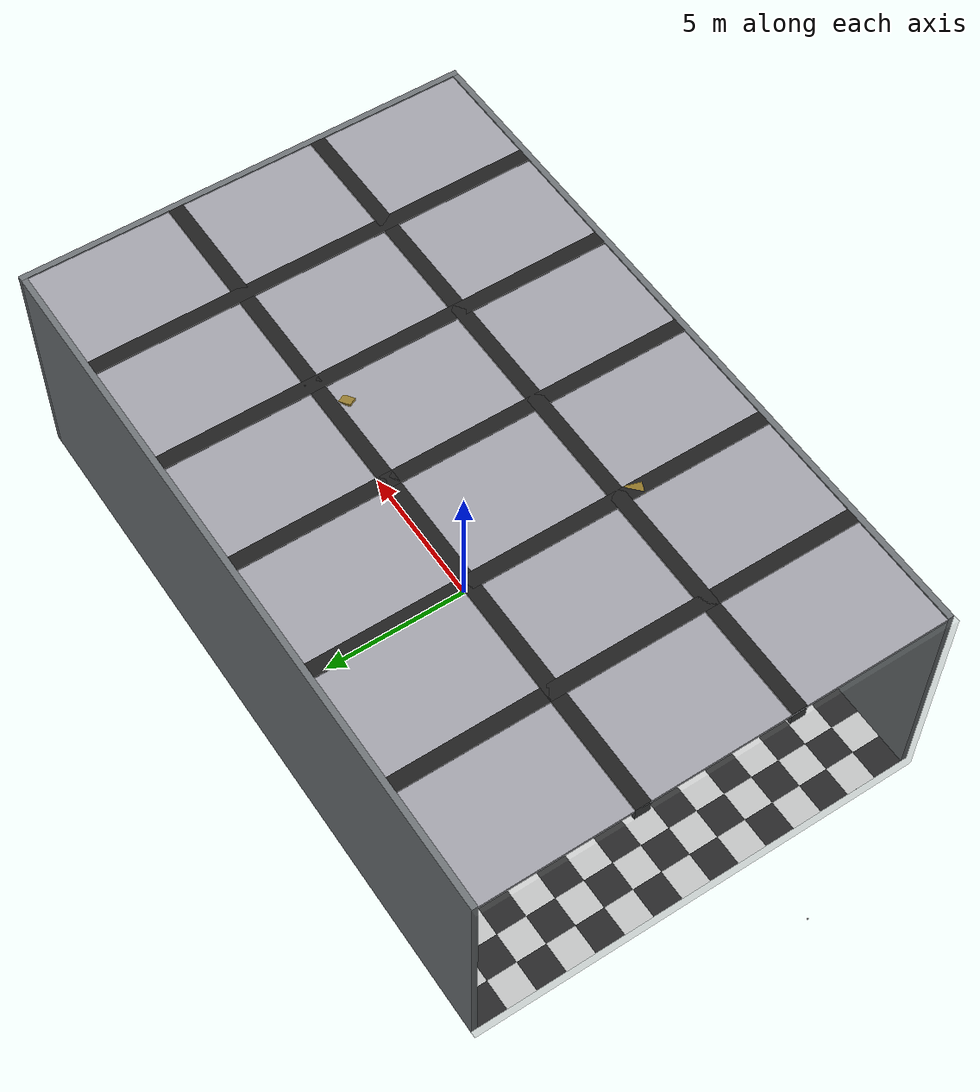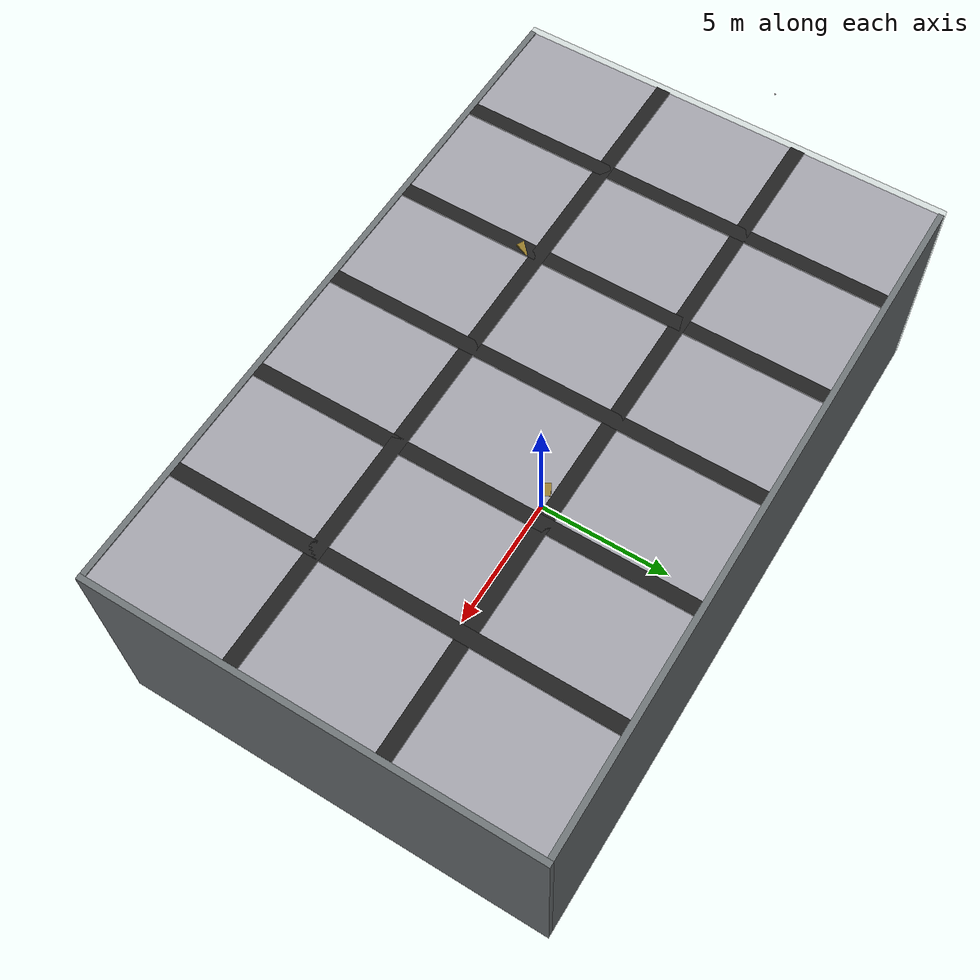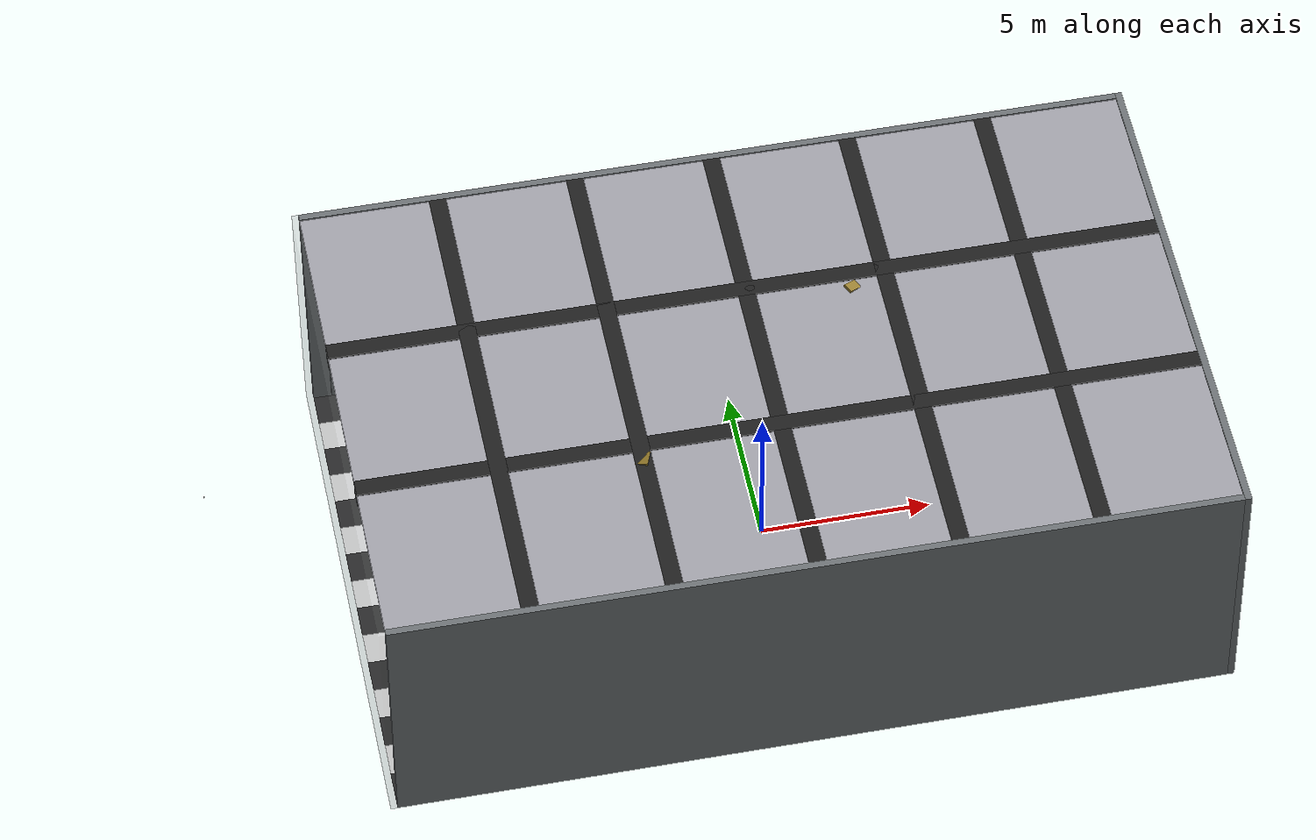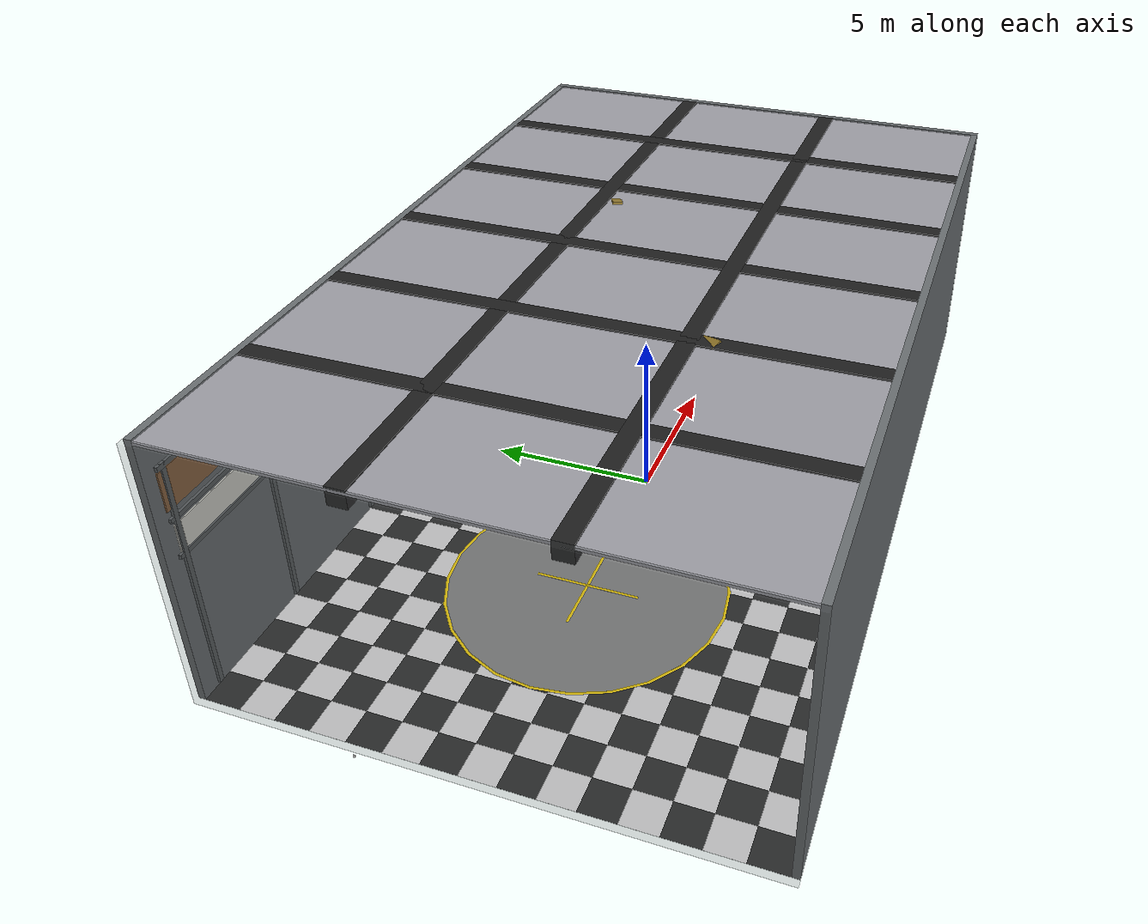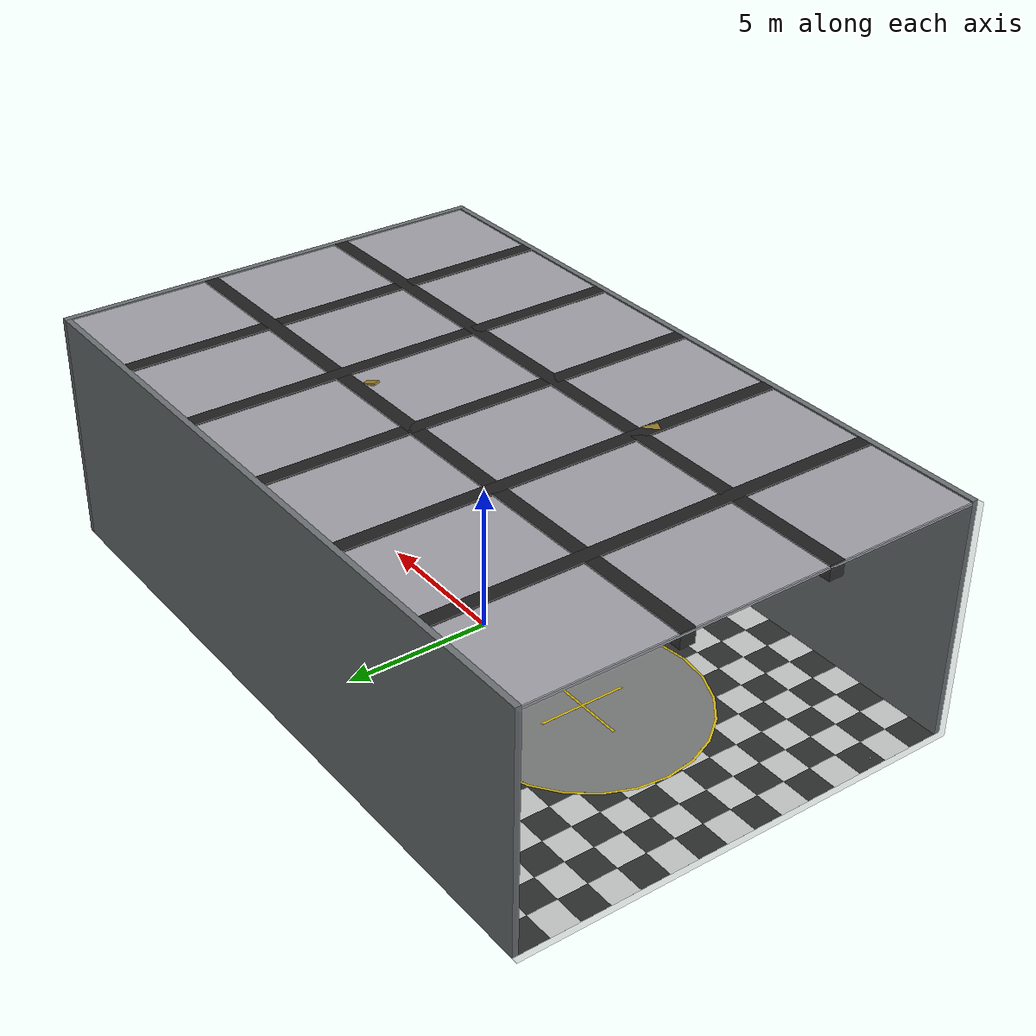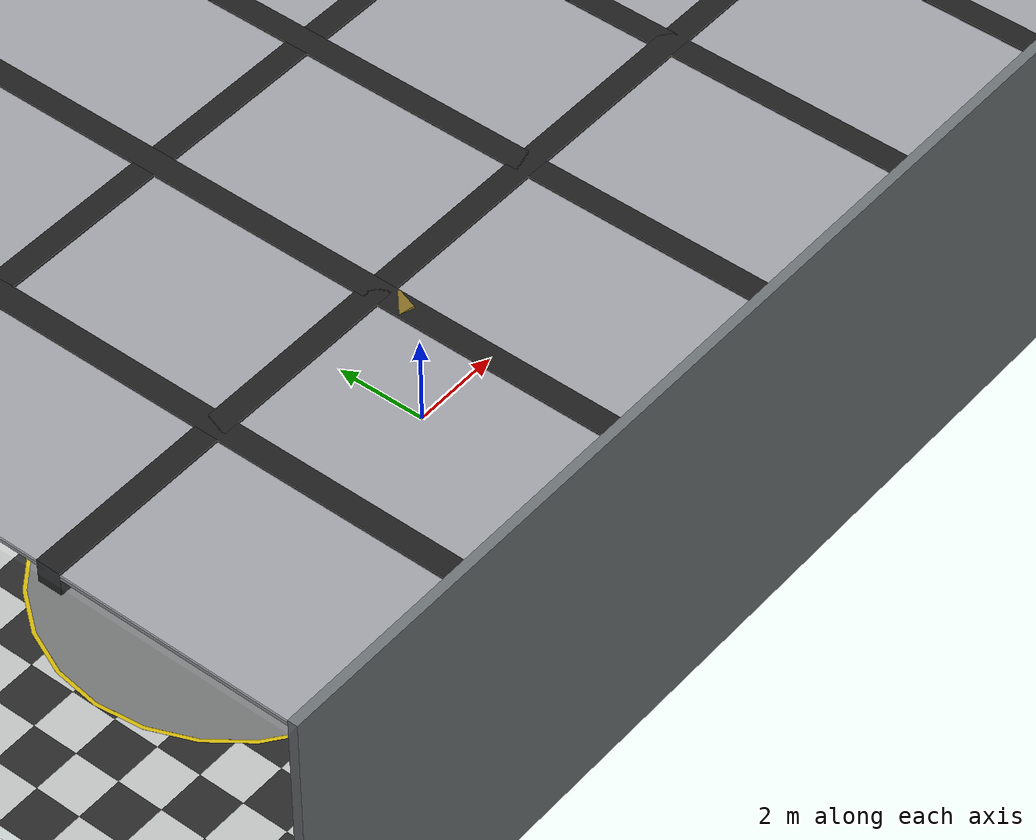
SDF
<sdf version="1.9">
 <world name="hangar_detailed">
  <physics type="ode">
   <max_step_size>0.004</max_step_size>
   <real_time_factor>1.0</real_time_factor>
   <real_time_update_rate>250</real_time_update_rate>
  </physics>
  <gravity>0 0 -9.8</gravity>
  <magnetic_field>6e-06 2.3e-05 -4.2e-05</magnetic_field>
  <atmosphere type="adiabatic"/>
  <scene>
   <grid>false</grid>
   <ambient>0.50 0.50 0.50 1</ambient>
   <background>0.35 0.35 0.35 1</background>
   <shadows>true</shadows>
  </scene>
  <model name="ground_plane">
   <static>true</static>
   <link name="link">
    <collision name="collision">
     <geometry><plane><normal>0 0 1</normal><size>24.0 15.0</size></plane></geometry>
    </collision>
   </link>
  </model>
  <model name="floor_tiles">
   <static>true</static>
   <pose>0 0 0.0015 0 0 0</pose>
   <link name="tiles">
    <visual name="t_00_00">
     <pose>-11.5 -7.0 0 0 0 0</pose>
     <geometry><box><size>1 1 0.001</size></box></geometry>
     <material><ambient>0.15 0.15 0.15 1</ambient><diffuse>0.15 0.15 0.15 1</diffuse></material>
    </visual>
    <visual name="t_00_01">
     <pose>-11.5 -6.0 0 0 0 0</pose>
     <geometry><box><size>1 1 0.001</size></box></geometry>
     <material><ambient>0.9 0.9 0.9 1</ambient><diffuse>0.9 0.9 0.9 1</diffuse></material>
    </visual>
    <visual name="t_00_02">
     <pose>-11.5 -5.0 0 0 0 0</pose>
     <geometry><box><size>1 1 0.001</size></box></geometry>
     <material><ambient>0.15 0.15 0.15 1</ambient><diffuse>0.15 0.15 0.15 1</diffuse></material>
    </visual>
    <visual name="t_00_03">
     <pose>-11.5 -4.0 0 0 0 0</pose>
     <geometry><box><size>1 1 0.001</size></box></geometry>
     <material><ambient>0.9 0.9 0.9 1</ambient><diffuse>0.9 0.9 0.9 1</diffuse></material>
    </visual>
    <visual name="t_00_04">
     <pose>-11.5 -3.0 0 0 0 0</pose>
     <geometry><box><size>1 1 0.001</size></box></geometry>
     <material><ambient>0.15 0.15 0.15 1</ambient><diffuse>0.15 0.15 0.15 1</diffuse></material>
    </visual>
    <visual name="t_00_05">
     <pose>-11.5 -2.0 0 0 0 0</pose>
     <geometry><box><size>1 1 0.001</size></box></geometry>
     <material><ambient>0.9 0.9 0.9 1</ambient><diffuse>0.9 0.9 0.9 1</diffuse></material>
    </visual>
    <visual name="t_00_06">
     <pose>-11.5 -1.0 0 0 0 0</pose>
     <geometry><box><size>1 1 0.001</size></box></geometry>
     <material><ambient>0.15 0.15 0.15 1</ambient><diffuse>0.15 0.15 0.15 1</diffuse></material>
    </visual>
    <visual name="t_00_07">
     <pose>-11.5 0.0 0 0 0 0</pose>
     <geometry><box><size>1 1 0.001</size></box></geometry>
     <material><ambient>0.9 0.9 0.9 1</ambient><diffuse>0.9 0.9 0.9 1</diffuse></material>
    </visual>
    <visual name="t_00_08">
     <pose>-11.5 1.0 0 0 0 0</pose>
     <geometry><box><size>1 1 0.001</size></box></geometry>
     <material><ambient>0.15 0.15 0.15 1</ambient><diffuse>0.15 0.15 0.15 1</diffuse></material>
    </visual>
    <visual name="t_00_09">
     <pose>-11.5 2.0 0 0 0 0</pose>
     <geometry><box><size>1 1 0.001</size></box></geometry>
     <material><ambient>0.9 0.9 0.9 1</ambient><diffuse>0.9 0.9 0.9 1</diffuse></material>
    </visual>
    <visual name="t_00_10">
     <pose>-11.5 3.0 0 0 0 0</pose>
     <geometry><box><size>1 1 0.001</size></box></geometry>
     <material><ambient>0.15 0.15 0.15 1</ambient><diffuse>0.15 0.15 0.15 1</diffuse></material>
    </visual>
    <visual name="t_00_11">
     <pose>-11.5 4.0 0 0 0 0</pose>
     <geometry><box><size>1 1 0.001</size></box></geometry>
     <material><ambient>0.9 0.9 0.9 1</ambient><diffuse>0.9 0.9 0.9 1</diffuse></material>
    </visual>
    <visual name="t_00_12">
     <pose>-11.5 5.0 0 0 0 0</pose>
     <geometry><box><size>1 1 0.001</size></box></geometry>
     <material><ambient>0.15 0.15 0.15 1</ambient><diffuse>0.15 0.15 0.15 1</diffuse></material>
    </visual>
    <visual name="t_00_13">
     <pose>-11.5 6.0 0 0 0 0</pose>
     <geometry><box><size>1 1 0.001</size></box></geometry>
     <material><ambient>0.9 0.9 0.9 1</ambient><diffuse>0.9 0.9 0.9 1</diffuse></material>
    </visual>
    <visual name="t_00_14">
     <pose>-11.5 7.0 0 0 0 0</pose>
     <geometry><box><size>1 1 0.001</size></box></geometry>
     <material><ambient>0.15 0.15 0.15 1</ambient><diffuse>0.15 0.15 0.15 1</diffuse></material>
    </visual>
    <visual name="t_01_00">
     <pose>-10.5 -7.0 0 0 0 0</pose>
     <geometry><box><size>1 1 0.001</size></box></geometry>
     <material><ambient>0.9 0.9 0.9 1</ambient><diffuse>0.9 0.9 0.9 1</diffuse></material>
    </visual>
    <visual name="t_01_01">
     <pose>-10.5 -6.0 0 0 0 0</pose>
     <geometry><box><size>1 1 0.001</size></box></geometry>
     <material><ambient>0.15 0.15 0.15 1</ambient><diffuse>0.15 0.15 0.15 1</diffuse></material>
    </visual>
    <visual name="t_01_02">
     <pose>-10.5 -5.0 0 0 0 0</pose>
     <geometry><box><size>1 1 0.001</size></box></geometry>
     <material><ambient>0.9 0.9 0.9 1</ambient><diffuse>0.9 0.9 0.9 1</diffuse></material>
    </visual>
    <visual name="t_01_03">
     <pose>-10.5 -4.0 0 0 0 0</pose>
     <geometry><box><size>1 1 0.001</size></box></geometry>
     <material><ambient>0.15 0.15 0.15 1</ambient><diffuse>0.15 0.15 0.15 1</diffuse></material>
    </visual>
    <visual name="t_01_04">
     <pose>-10.5 -3.0 0 0 0 0</pose>
     <geometry><box><size>1 1 0.001</size></box></geometry>
     <material><ambient>0.9 0.9 0.9 1</ambient><diffuse>0.9 0.9 0.9 1</diffuse></material>
    </visual>
    <visual name="t_01_05">
     <pose>-10.5 -2.0 0 0 0 0</pose>
     <geometry><box><size>1 1 0.001</size></box></geometry>
     <material><ambient>0.15 0.15 0.15 1</ambient><diffuse>0.15 0.15 0.15 1</diffuse></material>
    </visual>
    <visual name="t_01_06">
     <pose>-10.5 -1.0 0 0 0 0</pose>
     <geometry><box><size>1 1 0.001</size></box></geometry>
     <material><ambient>0.9 0.9 0.9 1</ambient><diffuse>0.9 0.9 0.9 1</diffuse></material>
    </visual>
    <visual name="t_01_07">
     <pose>-10.5 0.0 0 0 0 0</pose>
     <geometry><box><size>1 1 0.001</size></box></geometry>
     <material><ambient>0.15 0.15 0.15 1</ambient><diffuse>0.15 0.15 0.15 1</diffuse></material>
    </visual>
    <visual name="t_01_08">
     <pose>-10.5 1.0 0 0 0 0</pose>
     <geometry><box><size>1 1 0.001</size></box></geometry>
     <material><ambient>0.9 0.9 0.9 1</ambient><diffuse>0.9 0.9 0.9 1</diffuse></material>
    </visual>
    <visual name="t_01_09">
     <pose>-10.5 2.0 0 0 0 0</pose>
     <geometry><box><size>1 1 0.001</size></box></geometry>
     <material><ambient>0.15 0.15 0.15 1</ambient><diffuse>0.15 0.15 0.15 1</diffuse></material>
    </visual>
    <visual name="t_01_10">
     <pose>-10.5 3.0 0 0 0 0</pose>
     <geometry><box><size>1 1 0.001</size></box></geometry>
     <material><ambient>0.9 0.9 0.9 1</ambient><diffuse>0.9 0.9 0.9 1</diffuse></material>
    </visual>
    <visual name="t_01_11">
     <pose>-10.5 4.0 0 0 0 0</pose>
     <geometry><box><size>1 1 0.001</size></box></geometry>
     <material><ambient>0.15 0.15 0.15 1</ambient><diffuse>0.15 0.15 0.15 1</diffuse></material>
    </visual>
    <visual name="t_01_12">
     <pose>-10.5 5.0 0 0 0 0</pose>
     <geometry><box><size>1 1 0.001</size></box></geometry>
     <material><ambient>0.9 0.9 0.9 1</ambient><diffuse>0.9 0.9 0.9 1</diffuse></material>
    </visual>
    <visual name="t_01_13">
     <pose>-10.5 6.0 0 0 0 0</pose>
     <geometry><box><size>1 1 0.001</size></box></geometry>
     <material><ambient>0.15 0.15 0.15 1</ambient><diffuse>0.15 0.15 0.15 1</diffuse></material>
    </visual>
    <visual name="t_01_14">
     <pose>-10.5 7.0 0 0 0 0</pose>
     <geometry><box><size>1 1 0.001</size></box></geometry>
     <material><ambient>0.9 0.9 0.9 1</ambient><diffuse>0.9 0.9 0.9 1</diffuse></material>
    </visual>
    <visual name="t_02_00">
     <pose>-9.5 -7.0 0 0 0 0</pose>
     <geometry><box><size>1 1 0.001</size></box></geometry>
     <material><ambient>0.15 0.15 0.15 1</ambient><diffuse>0.15 0.15 0.15 1</diffuse></material>
    </visual>
    <visual name="t_02_01">
     <pose>-9.5 -6.0 0 0 0 0</pose>
     <geometry><box><size>1 1 0.001</size></box></geometry>
     <material><ambient>0.9 0.9 0.9 1</ambient><diffuse>0.9 0.9 0.9 1</diffuse></material>
    </visual>
    <visual name="t_02_02">
     <pose>-9.5 -5.0 0 0 0 0</pose>
     <geometry><box><size>1 1 0.001</size></box></geometry>
     <material><ambient>0.15 0.15 0.15 1</ambient><diffuse>0.15 0.15 0.15 1</diffuse></material>
    </visual>
    <visual name="t_02_03">
     <pose>-9.5 -4.0 0 0 0 0</pose>
     <geometry><box><size>1 1 0.001</size></box></geometry>
     <material><ambient>0.9 0.9 0.9 1</ambient><diffuse>0.9 0.9 0.9 1</diffuse></material>
    </visual>
    <visual name="t_02_04">
     <pose>-9.5 -3.0 0 0 0 0</pose>
     <geometry><box><size>1 1 0.001</size></box></geometry>
     <material><ambient>0.15 0.15 0.15 1</ambient><diffuse>0.15 0.15 0.15 1</diffuse></material>
    </visual>
    <visual name="t_02_05">
     <pose>-9.5 -2.0 0 0 0 0</pose>
     <geometry><box><size>1 1 0.001</size></box></geometry>
     <material><ambient>0.9 0.9 0.9 1</ambient><diffuse>0.9 0.9 0.9 1</diffuse></material>
    </visual>
    <visual name="t_02_06">
     <pose>-9.5 -1.0 0 0 0 0</pose>
     <geometry><box><size>1 1 0.001</size></box></geometry>
     <material><ambient>0.15 0.15 0.15 1</ambient><diffuse>0.15 0.15 0.15 1</diffuse></material>
    </visual>
    <visual name="t_02_07">
     <pose>-9.5 0.0 0 0 0 0</pose>
     <geometry><box><size>1 1 0.001</size></box></geometry>
     <material><ambient>0.9 0.9 0.9 1</ambient><diffuse>0.9 0.9 0.9 1</diffuse></material>
    </visual>
    <visual name="t_02_08">
     <pose>-9.5 1.0 0 0 0 0</pose>
     <geometry><box><size>1 1 0.001</size></box></geometry>
     <material><ambient>0.15 0.15 0.15 1</ambient><diffuse>0.15 0.15 0.15 1</diffuse></material>
    </visual>
    <visual name="t_02_09">
     <pose>-9.5 2.0 0 0 0 0</pose>
     <geometry><box><size>1 1 0.001</size></box></geometry>
     <material><ambient>0.9 0.9 0.9 1</ambient><diffuse>0.9 0.9 0.9 1</diffuse></material>
    </visual>
    <visual name="t_02_10">
     <pose>-9.5 3.0 0 0 0 0</pose>
     <geometry><box><size>1 1 0.001</size></box></geometry>
     <material><ambient>0.15 0.15 0.15 1</ambient><diffuse>0.15 0.15 0.15 1</diffuse></material>
    </visual>
    <visual name="t_02_11">
     <pose>-9.5 4.0 0 0 0 0</pose>
     <geometry><box><size>1 1 0.001</size></box></geometry>
     <material><ambient>0.9 0.9 0.9 1</ambient><diffuse>0.9 0.9 0.9 1</diffuse></material>
    </visual>
    <visual name="t_02_12">
     <pose>-9.5 5.0 0 0 0 0</pose>
     <geometry><box><size>1 1 0.001</size></box></geometry>
     <material><ambient>0.15 0.15 0.15 1</ambient><diffuse>0.15 0.15 0.15 1</diffuse></material>
    </visual>
    <visual name="t_02_13">
     <pose>-9.5 6.0 0 0 0 0</pose>
     <geometry><box><size>1 1 0.001</size></box></geometry>
     <material><ambient>0.9 0.9 0.9 1</ambient><diffuse>0.9 0.9 0.9 1</diffuse></material>
    </visual>
    <visual name="t_02_14">
     <pose>-9.5 7.0 0 0 0 0</pose>
     <geometry><box><size>1 1 0.001</size></box></geometry>
     <material><ambient>0.15 0.15 0.15 1</ambient><diffuse>0.15 0.15 0.15 1</diffuse></material>
    </visual>
    <visual name="t_03_00">
     <pose>-8.5 -7.0 0 0 0 0</pose>
     <geometry><box><size>1 1 0.001</size></box></geometry>
     <material><ambient>0.9 0.9 0.9 1</ambient><diffuse>0.9 0.9 0.9 1</diffuse></material>
    </visual>
    <visual name="t_03_01">
     <pose>-8.5 -6.0 0 0 0 0</pose>
     <geometry><box><size>1 1 0.001</size></box></geometry>
     <material><ambient>0.15 0.15 0.15 1</ambient><diffuse>0.15 0.15 0.15 1</diffuse></material>
    </visual>
    <visual name="t_03_02">
     <pose>-8.5 -5.0 0 0 0 0</pose>
     <geometry><box><size>1 1 0.001</size></box></geometry>
     <material><ambient>0.9 0.9 0.9 1</ambient><diffuse>0.9 0.9 0.9 1</diffuse></material>
    </visual>
    <visual name="t_03_03">
     <pose>-8.5 -4.0 0 0 0 0</pose>
     <geometry><box><size>1 1 0.001</size></box></geometry>
     <material><ambient>0.15 0.15 0.15 1</ambient><diffuse>0.15 0.15 0.15 1</diffuse></material>
    </visual>
    <visual name="t_03_04">
     <pose>-8.5 -3.0 0 0 0 0</pose>
     <geometry><box><size>1 1 0.001</size></box></geometry>
     <material><ambient>0.9 0.9 0.9 1</ambient><diffuse>0.9 0.9 0.9 1</diffuse></material>
    </visual>
    <visual name="t_03_05">
     <pose>-8.5 -2.0 0 0 0 0</pose>
     <geometry><box><size>1 1 0.001</size></box></geometry>
     <material><ambient>0.15 0.15 0.15 1</ambient><diffuse>0.15 0.15 0.15 1</diffuse></material>
    </visual>
    <visual name="t_03_06">
     <pose>-8.5 -1.0 0 0 0 0</pose>
     <geometry><box><size>1 1 0.001</size></box></geometry>
     <material><ambient>0.9 0.9 0.9 1</ambient><diffuse>0.9 0.9 0.9 1</diffuse></material>
    </visual>
    <visual name="t_03_07">
     <pose>-8.5 0.0 0 0 0 0</pose>
     <geometry><box><size>1 1 0.001</size></box></geometry>
     <material><ambient>0.15 0.15 0.15 1</ambient><diffuse>0.15 0.15 0.15 1</diffuse></material>
    </visual>
    <visual name="t_03_08">
     <pose>-8.5 1.0 0 0 0 0</pose>
     <geometry><box><size>1 1 0.001</size></box></geometry>
     <material><ambient>0.9 0.9 0.9 1</ambient><diffuse>0.9 0.9 0.9 1</diffuse></material>
    </visual>
    <visual name="t_03_09">
     <pose>-8.5 2.0 0 0 0 0</pose>
     <geometry><box><size>1 1 0.001</size></box></geometry>
     <material><ambient>0.15 0.15 0.15 1</ambient><diffuse>0.15 0.15 0.15 1</diffuse></material>
    </visual>
    <visual name="t_03_10">
     <pose>-8.5 3.0 0 0 0 0</pose>
     <geometry><box><size>1 1 0.001</size></box></geometry>
     <material><ambient>0.9 0.9 0.9 1</ambient><diffuse>0.9 0.9 0.9 1</diffuse></material>
    </visual>
    <visual name="t_03_11">
     <pose>-8.5 4.0 0 0 0 0</pose>
     <geometry><box><size>1 1 0.001</size></box></geometry>
     <material><ambient>0.15 0.15 0.15 1</ambient><diffuse>0.15 0.15 0.15 1</diffuse></material>
    </visual>
    <visual name="t_03_12">
     <pose>-8.5 5.0 0 0 0 0</pose>
     <geometry><box><size>1 1 0.001</size></box></geometry>
     <material><ambient>0.9 0.9 0.9 1</ambient><diffuse>0.9 0.9 0.9 1</diffuse></material>
    </visual>
    <visual name="t_03_13">
     <pose>-8.5 6.0 0 0 0 0</pose>
     <geometry><box><size>1 1 0.001</size></box></geometry>
     <material><ambient>0.15 0.15 0.15 1</ambient><diffuse>0.15 0.15 0.15 1</diffuse></material>
    </visual>
    <visual name="t_03_14">
     <pose>-8.5 7.0 0 0 0 0</pose>
     <geometry><box><size>1 1 0.001</size></box></geometry>
     <material><ambient>0.9 0.9 0.9 1</ambient><diffuse>0.9 0.9 0.9 1</diffuse></material>
    </visual>
    <visual name="t_04_00">
     <pose>-7.5 -7.0 0 0 0 0</pose>
     <geometry><box><size>1 1 0.001</size></box></geometry>
     <material><ambient>0.15 0.15 0.15 1</ambient><diffuse>0.15 0.15 0.15 1</diffuse></material>
    </visual>
    <visual name="t_04_01">
     <pose>-7.5 -6.0 0 0 0 0</pose>
     <geometry><box><size>1 1 0.001</size></box></geometry>
     <material><ambient>0.9 0.9 0.9 1</ambient><diffuse>0.9 0.9 0.9 1</diffuse></material>
    </visual>
    <visual name="t_04_02">
     <pose>-7.5 -5.0 0 0 0 0</pose>
     <geometry><box><size>1 1 0.001</size></box></geometry>
     <material><ambient>0.15 0.15 0.15 1</ambient><diffuse>0.15 0.15 0.15 1</diffuse></material>
    </visual>
    <visual name="t_04_03">
     <pose>-7.5 -4.0 0 0 0 0</pose>
     <geometry><box><size>1 1 0.001</size></box></geometry>
     <material><ambient>0.9 0.9 0.9 1</ambient><diffuse>0.9 0.9 0.9 1</diffuse></material>
    </visual>
    <visual name="t_04_04">
     <pose>-7.5 -3.0 0 0 0 0</pose>
     <geometry><box><size>1 1 0.001</size></box></geometry>
     <material><ambient>0.15 0.15 0.15 1</ambient><diffuse>0.15 0.15 0.15 1</diffuse></material>
    </visual>
    <visual name="t_04_05">
     <pose>-7.5 -2.0 0 0 0 0</pose>
     <geometry><box><size>1 1 0.001</size></box></geometry>
     <material><ambient>0.9 0.9 0.9 1</ambient><diffuse>0.9 0.9 0.9 1</diffuse></material>
    </visual>
    <visual name="t_04_06">
     <pose>-7.5 -1.0 0 0 0 0</pose>
     <geometry><box><size>1 1 0.001</size></box></geometry>
     <material><ambient>0.15 0.15 0.15 1</ambient><diffuse>0.15 0.15 0.15 1</diffuse></material>
    </visual>
    <visual name="t_04_07">
     <pose>-7.5 0.0 0 0 0 0</pose>
     <geometry><box><size>1 1 0.001</size></box></geometry>
     <material><ambient>0.9 0.9 0.9 1</ambient><diffuse>0.9 0.9 0.9 1</diffuse></material>
    </visual>
    <visual name="t_04_08">
     <pose>-7.5 1.0 0 0 0 0</pose>
     <geometry><box><size>1 1 0.001</size></box></geometry>
     <material><ambient>0.15 0.15 0.15 1</ambient><diffuse>0.15 0.15 0.15 1</diffuse></material>
    </visual>
    <visual name="t_04_09">
     <pose>-7.5 2.0 0 0 0 0</pose>
     <geometry><box><size>1 1 0.001</size></box></geometry>
     <material><ambient>0.9 0.9 0.9 1</ambient><diffuse>0.9 0.9 0.9 1</diffuse></material>
    </visual>
    <visual name="t_04_10">
     <pose>-7.5 3.0 0 0 0 0</pose>
     <geometry><box><size>1 1 0.001</size></box></geometry>
     <material><ambient>0.15 0.15 0.15 1</ambient><diffuse>0.15 0.15 0.15 1</diffuse></material>
    </visual>
    <visual name="t_04_11">
     <pose>-7.5 4.0 0 0 0 0</pose>
     <geometry><box><size>1 1 0.001</size></box></geometry>
     <material><ambient>0.9 0.9 0.9 1</ambient><diffuse>0.9 0.9 0.9 1</diffuse></material>
    </visual>
    <visual name="t_04_12">
     <pose>-7.5 5.0 0 0 0 0</pose>
     <geometry><box><size>1 1 0.001</size></box></geometry>
     <material><ambient>0.15 0.15 0.15 1</ambient><diffuse>0.15 0.15 0.15 1</diffuse></material>
    </visual>
    <visual name="t_04_13">
     <pose>-7.5 6.0 0 0 0 0</pose>
     <geometry><box><size>1 1 0.001</size></box></geometry>
     <material><ambient>0.9 0.9 0.9 1</ambient><diffuse>0.9 0.9 0.9 1</diffuse></material>
    </visual>
    <visual name="t_04_14">
     <pose>-7.5 7.0 0 0 0 0</pose>
     <geometry><box><size>1 1 0.001</size></box></geometry>
     <material><ambient>0.15 0.15 0.15 1</ambient><diffuse>0.15 0.15 0.15 1</diffuse></material>
    </visual>
    <visual name="t_05_00">
     <pose>-6.5 -7.0 0 0 0 0</pose>
     <geometry><box><size>1 1 0.001</size></box></geometry>
     <material><ambient>0.9 0.9 0.9 1</ambient><diffuse>0.9 0.9 0.9 1</diffuse></material>
    </visual>
    <visual name="t_05_01">
     <pose>-6.5 -6.0 0 0 0 0</pose>
     <geometry><box><size>1 1 0.001</size></box></geometry>
     <material><ambient>0.15 0.15 0.15 1</ambient><diffuse>0.15 0.15 0.15 1</diffuse></material>
    </visual>
    <visual name="t_05_02">
     <pose>-6.5 -5.0 0 0 0 0</pose>
     <geometry><box><size>1 1 0.001</size></box></geometry>
     <material><ambient>0.9 0.9 0.9 1</ambient><diffuse>0.9 0.9 0.9 1</diffuse></material>
    </visual>
    <visual name="t_05_03">
     <pose>-6.5 -4.0 0 0 0 0</pose>
     <geometry><box><size>1 1 0.001</size></box></geometry>
     <material><ambient>0.15 0.15 0.15 1</ambient><diffuse>0.15 0.15 0.15 1</diffuse></material>
    </visual>
    <visual name="t_05_04">
     <pose>-6.5 -3.0 0 0 0 0</pose>
     <geometry><box><size>1 1 0.001</size></box></geometry>
     <material><ambient>0.9 0.9 0.9 1</ambient><diffuse>0.9 0.9 0.9 1</diffuse></material>
    </visual>
    <visual name="t_05_05">
     <pose>-6.5 -2.0 0 0 0 0</pose>
     <geometry><box><size>1 1 0.001</size></box></geometry>
     <material><ambient>0.15 0.15 0.15 1</ambient><diffuse>0.15 0.15 0.15 1</diffuse></material>
    </visual>
    <visual name="t_05_06">
     <pose>-6.5 -1.0 0 0 0 0</pose>
     <geometry><box><size>1 1 0.001</size></box></geometry>
     <material><ambient>0.9 0.9 0.9 1</ambient><diffuse>0.9 0.9 0.9 1</diffuse></material>
    </visual>
    <visual name="t_05_07">
     <pose>-6.5 0.0 0 0 0 0</pose>
     <geometry><box><size>1 1 0.001</size></box></geometry>
     <material><ambient>0.15 0.15 0.15 1</ambient><diffuse>0.15 0.15 0.15 1</diffuse></material>
    </visual>
    <visual name="t_05_08">
     <pose>-6.5 1.0 0 0 0 0</pose>
     <geometry><box><size>1 1 0.001</size></box></geometry>
     <material><ambient>0.9 0.9 0.9 1</ambient><diffuse>0.9 0.9 0.9 1</diffuse></material>
    </visual>
    <visual name="t_05_09">
     <pose>-6.5 2.0 0 0 0 0</pose>
     <geometry><box><size>1 1 0.001</size></box></geometry>
     <material><ambient>0.15 0.15 0.15 1</ambient><diffuse>0.15 0.15 0.15 1</diffuse></material>
    </visual>
    <visual name="t_05_10">
     <pose>-6.5 3.0 0 0 0 0</pose>
     <geometry><box><size>1 1 0.001</size></box></geometry>
     <material><ambient>0.9 0.9 0.9 1</ambient><diffuse>0.9 0.9 0.9 1</diffuse></material>
    </visual>
    <visual name="t_05_11">
     <pose>-6.5 4.0 0 0 0 0</pose>
     <geometry><box><size>1 1 0.001</size></box></geometry>
     <material><ambient>0.15 0.15 0.15 1</ambient><diffuse>0.15 0.15 0.15 1</diffuse></material>
    </visual>
    <visual name="t_05_12">
     <pose>-6.5 5.0 0 0 0 0</pose>
     <geometry><box><size>1 1 0.001</size></box></geometry>
     <material><ambient>0.9 0.9 0.9 1</ambient><diffuse>0.9 0.9 0.9 1</diffuse></material>
    </visual>
    <visual name="t_05_13">
     <pose>-6.5 6.0 0 0 0 0</pose>
     <geometry><box><size>1 1 0.001</size></box></geometry>
     <material><ambient>0.15 0.15 0.15 1</ambient><diffuse>0.15 0.15 0.15 1</diffuse></material>
    </visual>
    <visual name="t_05_14">
     <pose>-6.5 7.0 0 0 0 0</pose>
     <geometry><box><size>1 1 0.001</size></box></geometry>
     <material><ambient>0.9 0.9 0.9 1</ambient><diffuse>0.9 0.9 0.9 1</diffuse></material>
    </visual>
    <visual name="t_06_00">
     <pose>-5.5 -7.0 0 0 0 0</pose>
     <geometry><box><size>1 1 0.001</size></box></geometry>
     <material><ambient>0.15 0.15 0.15 1</ambient><diffuse>0.15 0.15 0.15 1</diffuse></material>
    </visual>
    <visual name="t_06_01">
     <pose>-5.5 -6.0 0 0 0 0</pose>
     <geometry><box><size>1 1 0.001</size></box></geometry>
     <material><ambient>0.9 0.9 0.9 1</ambient><diffuse>0.9 0.9 0.9 1</diffuse></material>
    </visual>
    <visual name="t_06_02">
     <pose>-5.5 -5.0 0 0 0 0</pose>
     <geometry><box><size>1 1 0.001</size></box></geometry>
     <material><ambient>0.15 0.15 0.15 1</ambient><diffuse>0.15 0.15 0.15 1</diffuse></material>
    </visual>
    <visual name="t_06_03">
     <pose>-5.5 -4.0 0 0 0 0</pose>
     <geometry><box><size>1 1 0.001</size></box></geometry>
     <material><ambient>0.9 0.9 0.9 1</ambient><diffuse>0.9 0.9 0.9 1</diffuse></material>
    </visual>
    <visual name="t_06_04">
     <pose>-5.5 -3.0 0 0 0 0</pose>
     <geometry><box><size>1 1 0.001</size></box></geometry>
     <material><ambient>0.15 0.15 0.15 1</ambient><diffuse>0.15 0.15 0.15 1</diffuse></material>
    </visual>
    <visual name="t_06_05">
     <pose>-5.5 -2.0 0 0 0 0</pose>
     <geometry><box><size>1 1 0.001</size></box></geometry>
     <material><ambient>0.9 0.9 0.9 1</ambient><diffuse>0.9 0.9 0.9 1</diffuse></material>
    </visual>
    <visual name="t_06_06">
     <pose>-5.5 -1.0 0 0 0 0</pose>
     <geometry><box><size>1 1 0.001</size></box></geometry>
     <material><ambient>0.15 0.15 0.15 1</ambient><diffuse>0.15 0.15 0.15 1</diffuse></material>
    </visual>
    <visual name="t_06_07">
     <pose>-5.5 0.0 0 0 0 0</pose>
     <geometry><box><size>1 1 0.001</size></box></geometry>
     <material><ambient>0.9 0.9 0.9 1</ambient><diffuse>0.9 0.9 0.9 1</diffuse></material>
    </visual>
    <visual name="t_06_08">
     <pose>-5.5 1.0 0 0 0 0</pose>
     <geometry><box><size>1 1 0.001</size></box></geometry>
     <material><ambient>0.15 0.15 0.15 1</ambient><diffuse>0.15 0.15 0.15 1</diffuse></material>
    </visual>
    <visual name="t_06_09">
     <pose>-5.5 2.0 0 0 0 0</pose>
     <geometry><box><size>1 1 0.001</size></box></geometry>
     <material><ambient>0.9 0.9 0.9 1</ambient><diffuse>0.9 0.9 0.9 1</diffuse></material>
    </visual>
    <visual name="t_06_10">
     <pose>-5.5 3.0 0 0 0 0</pose>
     <geometry><box><size>1 1 0.001</size></box></geometry>
     <material><ambient>0.15 0.15 0.15 1</ambient><diffuse>0.15 0.15 0.15 1</diffuse></material>
    </visual>
    <visual name="t_06_11">
     <pose>-5.5 4.0 0 0 0 0</pose>
     <geometry><box><size>1 1 0.001</size></box></geometry>
     <material><ambient>0.9 0.9 0.9 1</ambient><diffuse>0.9 0.9 0.9 1</diffuse></material>
    </visual>
    <visual name="t_06_12">
     <pose>-5.5 5.0 0 0 0 0</pose>
     <geometry><box><size>1 1 0.001</size></box></geometry>
     <material><ambient>0.15 0.15 0.15 1</ambient><diffuse>0.15 0.15 0.15 1</diffuse></material>
    </visual>
    <visual name="t_06_13">
     <pose>-5.5 6.0 0 0 0 0</pose>
     <geometry><box><size>1 1 0.001</size></box></geometry>
     <material><ambient>0.9 0.9 0.9 1</ambient><diffuse>0.9 0.9 0.9 1</diffuse></material>
    </visual>
    <visual name="t_06_14">
     <pose>-5.5 7.0 0 0 0 0</pose>
     <geometry><box><size>1 1 0.001</size></box></geometry>
     <material><ambient>0.15 0.15 0.15 1</ambient><diffuse>0.15 0.15 0.15 1</diffuse></material>
    </visual>
    <visual name="t_07_00">
     <pose>-4.5 -7.0 0 0 0 0</pose>
     <geometry><box><size>1 1 0.001</size></box></geometry>
     <material><ambient>0.9 0.9 0.9 1</ambient><diffuse>0.9 0.9 0.9 1</diffuse></material>
    </visual>
    <visual name="t_07_01">
     <pose>-4.5 -6.0 0 0 0 0</pose>
     <geometry><box><size>1 1 0.001</size></box></geometry>
     <material><ambient>0.15 0.15 0.15 1</ambient><diffuse>0.15 0.15 0.15 1</diffuse></material>
    </visual>
    <visual name="t_07_02">
     <pose>-4.5 -5.0 0 0 0 0</pose>
     <geometry><box><size>1 1 0.001</size></box></geometry>
     <material><ambient>0.9 0.9 0.9 1</ambient><diffuse>0.9 0.9 0.9 1</diffuse></material>
    </visual>
    <visual name="t_07_03">
     <pose>-4.5 -4.0 0 0 0 0</pose>
     <geometry><box><size>1 1 0.001</size></box></geometry>
     <material><ambient>0.15 0.15 0.15 1</ambient><diffuse>0.15 0.15 0.15 1</diffuse></material>
    </visual>
    <visual name="t_07_04">
     <pose>-4.5 -3.0 0 0 0 0</pose>
     <geometry><box><size>1 1 0.001</size></box></geometry>
     <material><ambient>0.9 0.9 0.9 1</ambient><diffuse>0.9 0.9 0.9 1</diffuse></material>
    </visual>
    <visual name="t_07_05">
     <pose>-4.5 -2.0 0 0 0 0</pose>
     <geometry><box><size>1 1 0.001</size></box></geometry>
     <material><ambient>0.15 0.15 0.15 1</ambient><diffuse>0.15 0.15 0.15 1</diffuse></material>
    </visual>
    <visual name="t_07_06">
     <pose>-4.5 -1.0 0 0 0 0</pose>
     <geometry><box><size>1 1 0.001</size></box></geometry>
     <material><ambient>0.9 0.9 0.9 1</ambient><diffuse>0.9 0.9 0.9 1</diffuse></material>
    </visual>
    <visual name="t_07_07">
     <pose>-4.5 0.0 0 0 0 0</pose>
     <geometry><box><size>1 1 0.001</size></box></geometry>
     <material><ambient>0.15 0.15 0.15 1</ambient><diffuse>0.15 0.15 0.15 1</diffuse></material>
    </visual>
    <visual name="t_07_08">
     <pose>-4.5 1.0 0 0 0 0</pose>
     <geometry><box><size>1 1 0.001</size></box></geometry>
     <material><ambient>0.9 0.9 0.9 1</ambient><diffuse>0.9 0.9 0.9 1</diffuse></material>
    </visual>
    <visual name="t_07_09">
     <pose>-4.5 2.0 0 0 0 0</pose>
     <geometry><box><size>1 1 0.001</size></box></geometry>
     <material><ambient>0.15 0.15 0.15 1</ambient><diffuse>0.15 0.15 0.15 1</diffuse></material>
    </visual>
    <visual name="t_07_10">
     <pose>-4.5 3.0 0 0 0 0</pose>
     <geometry><box><size>1 1 0.001</size></box></geometry>
     <material><ambient>0.9 0.9 0.9 1</ambient><diffuse>0.9 0.9 0.9 1</diffuse></material>
    </visual>
    <visual name="t_07_11">
     <pose>-4.5 4.0 0 0 0 0</pose>
     <geometry><box><size>1 1 0.001</size></box></geometry>
     <material><ambient>0.15 0.15 0.15 1</ambient><diffuse>0.15 0.15 0.15 1</diffuse></material>
    </visual>
    <visual name="t_07_12">
     <pose>-4.5 5.0 0 0 0 0</pose>
     <geometry><box><size>1 1 0.001</size></box></geometry>
     <material><ambient>0.9 0.9 0.9 1</ambient><diffuse>0.9 0.9 0.9 1</diffuse></material>
    </visual>
    <visual name="t_07_13">
     <pose>-4.5 6.0 0 0 0 0</pose>
     <geometry><box><size>1 1 0.001</size></box></geometry>
     <material><ambient>0.15 0.15 0.15 1</ambient><diffuse>0.15 0.15 0.15 1</diffuse></material>
    </visual>
    <visual name="t_07_14">
     <pose>-4.5 7.0 0 0 0 0</pose>
     <geometry><box><size>1 1 0.001</size></box></geometry>
     <material><ambient>0.9 0.9 0.9 1</ambient><diffuse>0.9 0.9 0.9 1</diffuse></material>
    </visual>
    <visual name="t_08_00">
     <pose>-3.5 -7.0 0 0 0 0</pose>
     <geometry><box><size>1 1 0.001</size></box></geometry>
     <material><ambient>0.15 0.15 0.15 1</ambient><diffuse>0.15 0.15 0.15 1</diffuse></material>
    </visual>
    <visual name="t_08_01">
     <pose>-3.5 -6.0 0 0 0 0</pose>
     <geometry><box><size>1 1 0.001</size></box></geometry>
     <material><ambient>0.9 0.9 0.9 1</ambient><diffuse>0.9 0.9 0.9 1</diffuse></material>
    </visual>
    <visual name="t_08_02">
     <pose>-3.5 -5.0 0 0 0 0</pose>
     <geometry><box><size>1 1 0.001</size></box></geometry>
     <material><ambient>0.15 0.15 0.15 1</ambient><diffuse>0.15 0.15 0.15 1</diffuse></material>
    </visual>
    <visual name="t_08_03">
     <pose>-3.5 -4.0 0 0 0 0</pose>
     <geometry><box><size>1 1 0.001</size></box></geometry>
     <material><ambient>0.9 0.9 0.9 1</ambient><diffuse>0.9 0.9 0.9 1</diffuse></material>
    </visual>
    <visual name="t_08_04">
     <pose>-3.5 -3.0 0 0 0 0</pose>
     <geometry><box><size>1 1 0.001</size></box></geometry>
     <material><ambient>0.15 0.15 0.15 1</ambient><diffuse>0.15 0.15 0.15 1</diffuse></material>
    </visual>
    <visual name="t_08_05">
     <pose>-3.5 -2.0 0 0 0 0</pose>
     <geometry><box><size>1 1 0.001</size></box></geometry>
     <material><ambient>0.9 0.9 0.9 1</ambient><diffuse>0.9 0.9 0.9 1</diffuse></material>
    </visual>
    <visual name="t_08_06">
     <pose>-3.5 -1.0 0 0 0 0</pose>
     <geometry><box><size>1 1 0.001</size></box></geometry>
     <material><ambient>0.15 0.15 0.15 1</ambient><diffuse>0.15 0.15 0.15 1</diffuse></material>
    </visual>
    <visual name="t_08_07">
     <pose>-3.5 0.0 0 0 0 0</pose>
     <geometry><box><size>1 1 0.001</size></box></geometry>
     <material><ambient>0.9 0.9 0.9 1</ambient><diffuse>0.9 0.9 0.9 1</diffuse></material>
    </visual>
    <visual name="t_08_08">
     <pose>-3.5 1.0 0 0 0 0</pose>
     <geometry><box><size>1 1 0.001</size></box></geometry>
     <material><ambient>0.15 0.15 0.15 1</ambient><diffuse>0.15 0.15 0.15 1</diffuse></material>
    </visual>
    <visual name="t_08_09">
     <pose>-3.5 2.0 0 0 0 0</pose>
     <geometry><box><size>1 1 0.001</size></box></geometry>
     <material><ambient>0.9 0.9 0.9 1</ambient><diffuse>0.9 0.9 0.9 1</diffuse></material>
    </visual>
    <visual name="t_08_10">
     <pose>-3.5 3.0 0 0 0 0</pose>
     <geometry><box><size>1 1 0.001</size></box></geometry>
     <material><ambient>0.15 0.15 0.15 1</ambient><diffuse>0.15 0.15 0.15 1</diffuse></material>
    </visual>
    <visual name="t_08_11">
     <pose>-3.5 4.0 0 0 0 0</pose>
     <geometry><box><size>1 1 0.001</size></box></geometry>
     <material><ambient>0.9 0.9 0.9 1</ambient><diffuse>0.9 0.9 0.9 1</diffuse></material>
    </visual>
    <visual name="t_08_12">
     <pose>-3.5 5.0 0 0 0 0</pose>
     <geometry><box><size>1 1 0.001</size></box></geometry>
     <material><ambient>0.15 0.15 0.15 1</ambient><diffuse>0.15 0.15 0.15 1</diffuse></material>
    </visual>
    <visual name="t_08_13">
     <pose>-3.5 6.0 0 0 0 0</pose>
     <geometry><box><size>1 1 0.001</size></box></geometry>
     <material><ambient>0.9 0.9 0.9 1</ambient><diffuse>0.9 0.9 0.9 1</diffuse></material>
    </visual>
    <visual name="t_08_14">
     <pose>-3.5 7.0 0 0 0 0</pose>
     <geometry><box><size>1 1 0.001</size></box></geometry>
     <material><ambient>0.15 0.15 0.15 1</ambient><diffuse>0.15 0.15 0.15 1</diffuse></material>
    </visual>
    <visual name="t_09_00">
     <pose>-2.5 -7.0 0 0 0 0</pose>
     <geometry><box><size>1 1 0.001</size></box></geometry>
     <material><ambient>0.9 0.9 0.9 1</ambient><diffuse>0.9 0.9 0.9 1</diffuse></material>
    </visual>
    <visual name="t_09_01">
     <pose>-2.5 -6.0 0 0 0 0</pose>
     <geometry><box><size>1 1 0.001</size></box></geometry>
     <material><ambient>0.15 0.15 0.15 1</ambient><diffuse>0.15 0.15 0.15 1</diffuse></material>
    </visual>
    <visual name="t_09_02">
     <pose>-2.5 -5.0 0 0 0 0</pose>
     <geometry><box><size>1 1 0.001</size></box></geometry>
     <material><ambient>0.9 0.9 0.9 1</ambient><diffuse>0.9 0.9 0.9 1</diffuse></material>
    </visual>
    <visual name="t_09_03">
     <pose>-2.5 -4.0 0 0 0 0</pose>
     <geometry><box><size>1 1 0.001</size></box></geometry>
     <material><ambient>0.15 0.15 0.15 1</ambient><diffuse>0.15 0.15 0.15 1</diffuse></material>
    </visual>
    <visual name="t_09_04">
     <pose>-2.5 -3.0 0 0 0 0</pose>
     <geometry><box><size>1 1 0.001</size></box></geometry>
     <material><ambient>0.9 0.9 0.9 1</ambient><diffuse>0.9 0.9 0.9 1</diffuse></material>
    </visual>
    <visual name="t_09_05">
     <pose>-2.5 -2.0 0 0 0 0</pose>
     <geometry><box><size>1 1 0.001</size></box></geometry>
     <material><ambient>0.15 0.15 0.15 1</ambient><diffuse>0.15 0.15 0.15 1</diffuse></material>
    </visual>
    <visual name="t_09_06">
     <pose>-2.5 -1.0 0 0 0 0</pose>
     <geometry><box><size>1 1 0.001</size></box></geometry>
     <material><ambient>0.9 0.9 0.9 1</ambient><diffuse>0.9 0.9 0.9 1</diffuse></material>
    </visual>
    <visual name="t_09_07">
     <pose>-2.5 0.0 0 0 0 0</pose>
     <geometry><box><size>1 1 0.001</size></box></geometry>
     <material><ambient>0.15 0.15 0.15 1</ambient><diffuse>0.15 0.15 0.15 1</diffuse></material>
    </visual>
    <visual name="t_09_08">
     <pose>-2.5 1.0 0 0 0 0</pose>
     <geometry><box><size>1 1 0.001</size></box></geometry>
     <material><ambient>0.9 0.9 0.9 1</ambient><diffuse>0.9 0.9 0.9 1</diffuse></material>
    </visual>
    <visual name="t_09_09">
     <pose>-2.5 2.0 0 0 0 0</pose>
     <geometry><box><size>1 1 0.001</size></box></geometry>
     <material><ambient>0.15 0.15 0.15 1</ambient><diffuse>0.15 0.15 0.15 1</diffuse></material>
    </visual>
    <visual name="t_09_10">
     <pose>-2.5 3.0 0 0 0 0</pose>
     <geometry><box><size>1 1 0.001</size></box></geometry>
     <material><ambient>0.9 0.9 0.9 1</ambient><diffuse>0.9 0.9 0.9 1</diffuse></material>
    </visual>
    <visual name="t_09_11">
     <pose>-2.5 4.0 0 0 0 0</pose>
     <geometry><box><size>1 1 0.001</size></box></geometry>
     <material><ambient>0.15 0.15 0.15 1</ambient><diffuse>0.15 0.15 0.15 1</diffuse></material>
    </visual>
    <visual name="t_09_12">
     <pose>-2.5 5.0 0 0 0 0</pose>
     <geometry><box><size>1 1 0.001</size></box></geometry>
     <material><ambient>0.9 0.9 0.9 1</ambient><diffuse>0.9 0.9 0.9 1</diffuse></material>
    </visual>
    <visual name="t_09_13">
     <pose>-2.5 6.0 0 0 0 0</pose>
     <geometry><box><size>1 1 0.001</size></box></geometry>
     <material><ambient>0.15 0.15 0.15 1</ambient><diffuse>0.15 0.15 0.15 1</diffuse></material>
    </visual>
    <visual name="t_09_14">
     <pose>-2.5 7.0 0 0 0 0</pose>
     <geometry><box><size>1 1 0.001</size></box></geometry>
     <material><ambient>0.9 0.9 0.9 1</ambient><diffuse>0.9 0.9 0.9 1</diffuse></material>
    </visual>
    <visual name="t_10_00">
     <pose>-1.5 -7.0 0 0 0 0</pose>
     <geometry><box><size>1 1 0.001</size></box></geometry>
     <material><ambient>0.15 0.15 0.15 1</ambient><diffuse>0.15 0.15 0.15 1</diffuse></material>
    </visual>
    <visual name="t_10_01">
     <pose>-1.5 -6.0 0 0 0 0</pose>
     <geometry><box><size>1 1 0.001</size></box></geometry>
     <material><ambient>0.9 0.9 0.9 1</ambient><diffuse>0.9 0.9 0.9 1</diffuse></material>
    </visual>
    <visual name="t_10_02">
     <pose>-1.5 -5.0 0 0 0 0</pose>
     <geometry><box><size>1 1 0.001</size></box></geometry>
     <material><ambient>0.15 0.15 0.15 1</ambient><diffuse>0.15 0.15 0.15 1</diffuse></material>
    </visual>
    <visual name="t_10_03">
     <pose>-1.5 -4.0 0 0 0 0</pose>
     <geometry><box><size>1 1 0.001</size></box></geometry>
     <material><ambient>0.9 0.9 0.9 1</ambient><diffuse>0.9 0.9 0.9 1</diffuse></material>
    </visual>
    <visual name="t_10_04">
     <pose>-1.5 -3.0 0 0 0 0</pose>
     <geometry><box><size>1 1 0.001</size></box></geometry>
     <material><ambient>0.15 0.15 0.15 1</ambient><diffuse>0.15 0.15 0.15 1</diffuse></material>
    </visual>
    <visual name="t_10_05">
     <pose>-1.5 -2.0 0 0 0 0</pose>
     <geometry><box><size>1 1 0.001</size></box></geometry>
     <material><ambient>0.9 0.9 0.9 1</ambient><diffuse>0.9 0.9 0.9 1</diffuse></material>
    </visual>
    <visual name="t_10_06">
     <pose>-1.5 -1.0 0 0 0 0</pose>
     <geometry><box><size>1 1 0.001</size></box></geometry>
     <material><ambient>0.15 0.15 0.15 1</ambient><diffuse>0.15 0.15 0.15 1</diffuse></material>
    </visual>
    <visual name="t_10_07">
     <pose>-1.5 0.0 0 0 0 0</pose>
     <geometry><box><size>1 1 0.001</size></box></geometry>
     <material><ambient>0.9 0.9 0.9 1</ambient><diffuse>0.9 0.9 0.9 1</diffuse></material>
    </visual>
    <visual name="t_10_08">
     <pose>-1.5 1.0 0 0 0 0</pose>
     <geometry><box><size>1 1 0.001</size></box></geometry>
     <material><ambient>0.15 0.15 0.15 1</ambient><diffuse>0.15 0.15 0.15 1</diffuse></material>
    </visual>
    <visual name="t_10_09">
     <pose>-1.5 2.0 0 0 0 0</pose>
     <geometry><box><size>1 1 0.001</size></box></geometry>
     <material><ambient>0.9 0.9 0.9 1</ambient><diffuse>0.9 0.9 0.9 1</diffuse></material>
    </visual>
    <visual name="t_10_10">
     <pose>-1.5 3.0 0 0 0 0</pose>
     <geometry><box><size>1 1 0.001</size></box></geometry>
     <material><ambient>0.15 0.15 0.15 1</ambient><diffuse>0.15 0.15 0.15 1</diffuse></material>
    </visual>
    <visual name="t_10_11">
     <pose>-1.5 4.0 0 0 0 0</pose>
     <geometry><box><size>1 1 0.001</size></box></geometry>
     <material><ambient>0.9 0.9 0.9 1</ambient><diffuse>0.9 0.9 0.9 1</diffuse></material>
    </visual>
    <visual name="t_10_12">
     <pose>-1.5 5.0 0 0 0 0</pose>
     <geometry><box><size>1 1 0.001</size></box></geometry>
     <material><ambient>0.15 0.15 0.15 1</ambient><diffuse>0.15 0.15 0.15 1</diffuse></material>
    </visual>
    <visual name="t_10_13">
     <pose>-1.5 6.0 0 0 0 0</pose>
     <geometry><box><size>1 1 0.001</size></box></geometry>
     <material><ambient>0.9 0.9 0.9 1</ambient><diffuse>0.9 0.9 0.9 1</diffuse></material>
    </visual>
    <visual name="t_10_14">
     <pose>-1.5 7.0 0 0 0 0</pose>
     <geometry><box><size>1 1 0.001</size></box></geometry>
     <material><ambient>0.15 0.15 0.15 1</ambient><diffuse>0.15 0.15 0.15 1</diffuse></material>
    </visual>
    <visual name="t_11_00">
     <pose>-0.5 -7.0 0 0 0 0</pose>
     <geometry><box><size>1 1 0.001</size></box></geometry>
     <material><ambient>0.9 0.9 0.9 1</ambient><diffuse>0.9 0.9 0.9 1</diffuse></material>
    </visual>
    <visual name="t_11_01">
     <pose>-0.5 -6.0 0 0 0 0</pose>
     <geometry><box><size>1 1 0.001</size></box></geometry>
     <material><ambient>0.15 0.15 0.15 1</ambient><diffuse>0.15 0.15 0.15 1</diffuse></material>
    </visual>
    <visual name="t_11_02">
     <pose>-0.5 -5.0 0 0 0 0</pose>
     <geometry><box><size>1 1 0.001</size></box></geometry>
     <material><ambient>0.9 0.9 0.9 1</ambient><diffuse>0.9 0.9 0.9 1</diffuse></material>
    </visual>
    <visual name="t_11_03">
     <pose>-0.5 -4.0 0 0 0 0</pose>
     <geometry><box><size>1 1 0.001</size></box></geometry>
     <material><ambient>0.15 0.15 0.15 1</ambient><diffuse>0.15 0.15 0.15 1</diffuse></material>
    </visual>
    <visual name="t_11_04">
     <pose>-0.5 -3.0 0 0 0 0</pose>
     <geometry><box><size>1 1 0.001</size></box></geometry>
     <material><ambient>0.9 0.9 0.9 1</ambient><diffuse>0.9 0.9 0.9 1</diffuse></material>
    </visual>
    <visual name="t_11_05">
     <pose>-0.5 -2.0 0 0 0 0</pose>
     <geometry><box><size>1 1 0.001</size></box></geometry>
     <material><ambient>0.15 0.15 0.15 1</ambient><diffuse>0.15 0.15 0.15 1</diffuse></material>
    </visual>
    <visual name="t_11_06">
     <pose>-0.5 -1.0 0 0 0 0</pose>
     <geometry><box><size>1 1 0.001</size></box></geometry>
     <material><ambient>0.9 0.9 0.9 1</ambient><diffuse>0.9 0.9 0.9 1</diffuse></material>
    </visual>
    <visual name="t_11_07">
     <pose>-0.5 0.0 0 0 0 0</pose>
     <geometry><box><size>1 1 0.001</size></box></geometry>
     <material><ambient>0.15 0.15 0.15 1</ambient><diffuse>0.15 0.15 0.15 1</diffuse></material>
    </visual>
    <visual name="t_11_08">
     <pose>-0.5 1.0 0 0 0 0</pose>
     <geometry><box><size>1 1 0.001</size></box></geometry>
     <material><ambient>0.9 0.9 0.9 1</ambient><diffuse>0.9 0.9 0.9 1</diffuse></material>
    </visual>
    <visual name="t_11_09">
     <pose>-0.5 2.0 0 0 0 0</pose>
     <geometry><box><size>1 1 0.001</size></box></geometry>
     <material><ambient>0.15 0.15 0.15 1</ambient><diffuse>0.15 0.15 0.15 1</diffuse></material>
    </visual>
    <visual name="t_11_10">
     <pose>-0.5 3.0 0 0 0 0</pose>
     <geometry><box><size>1 1 0.001</size></box></geometry>
     <material><ambient>0.9 0.9 0.9 1</ambient><diffuse>0.9 0.9 0.9 1</diffuse></material>
    </visual>
    <visual name="t_11_11">
     <pose>-0.5 4.0 0 0 0 0</pose>
     <geometry><box><size>1 1 0.001</size></box></geometry>
     <material><ambient>0.15 0.15 0.15 1</ambient><diffuse>0.15 0.15 0.15 1</diffuse></material>
    </visual>
    <visual name="t_11_12">
     <pose>-0.5 5.0 0 0 0 0</pose>
     <geometry><box><size>1 1 0.001</size></box></geometry>
     <material><ambient>0.9 0.9 0.9 1</ambient><diffuse>0.9 0.9 0.9 1</diffuse></material>
    </visual>
    <visual name="t_11_13">
     <pose>-0.5 6.0 0 0 0 0</pose>
     <geometry><box><size>1 1 0.001</size></box></geometry>
     <material><ambient>0.15 0.15 0.15 1</ambient><diffuse>0.15 0.15 0.15 1</diffuse></material>
    </visual>
    <visual name="t_11_14">
     <pose>-0.5 7.0 0 0 0 0</pose>
     <geometry><box><size>1 1 0.001</size></box></geometry>
     <material><ambient>0.9 0.9 0.9 1</ambient><diffuse>0.9 0.9 0.9 1</diffuse></material>
    </visual>
    <visual name="t_12_00">
     <pose>0.5 -7.0 0 0 0 0</pose>
     <geometry><box><size>1 1 0.001</size></box></geometry>
     <material><ambient>0.15 0.15 0.15 1</ambient><diffuse>0.15 0.15 0.15 1</diffuse></material>
    </visual>
    <visual name="t_12_01">
     <pose>0.5 -6.0 0 0 0 0</pose>
     <geometry><box><size>1 1 0.001</size></box></geometry>
     <material><ambient>0.9 0.9 0.9 1</ambient><diffuse>0.9 0.9 0.9 1</diffuse></material>
    </visual>
    <visual name="t_12_02">
     <pose>0.5 -5.0 0 0 0 0</pose>
     <geometry><box><size>1 1 0.001</size></box></geometry>
     <material><ambient>0.15 0.15 0.15 1</ambient><diffuse>0.15 0.15 0.15 1</diffuse></material>
    </visual>
    <visual name="t_12_03">
     <pose>0.5 -4.0 0 0 0 0</pose>
     <geometry><box><size>1 1 0.001</size></box></geometry>
     <material><ambient>0.9 0.9 0.9 1</ambient><diffuse>0.9 0.9 0.9 1</diffuse></material>
    </visual>
    <visual name="t_12_04">
     <pose>0.5 -3.0 0 0 0 0</pose>
     <geometry><box><size>1 1 0.001</size></box></geometry>
     <material><ambient>0.15 0.15 0.15 1</ambient><diffuse>0.15 0.15 0.15 1</diffuse></material>
    </visual>
    <visual name="t_12_05">
     <pose>0.5 -2.0 0 0 0 0</pose>
     <geometry><box><size>1 1 0.001</size></box></geometry>
     <material><ambient>0.9 0.9 0.9 1</ambient><diffuse>0.9 0.9 0.9 1</diffuse></material>
    </visual>
    <visual name="t_12_06">
     <pose>0.5 -1.0 0 0 0 0</pose>
     <geometry><box><size>1 1 0.001</size></box></geometry>
     <material><ambient>0.15 0.15 0.15 1</ambient><diffuse>0.15 0.15 0.15 1</diffuse></material>
    </visual>
    <visual name="t_12_07">
     <pose>0.5 0.0 0 0 0 0</pose>
     <geometry><box><size>1 1 0.001</size></box></geometry>
     <material><ambient>0.9 0.9 0.9 1</ambient><diffuse>0.9 0.9 0.9 1</diffuse></material>
    </visual>
    <visual name="t_12_08">
     <pose>0.5 1.0 0 0 0 0</pose>
     <geometry><box><size>1 1 0.001</size></box></geometry>
     <material><ambient>0.15 0.15 0.15 1</ambient><diffuse>0.15 0.15 0.15 1</diffuse></material>
    </visual>
    <visual name="t_12_09">
     <pose>0.5 2.0 0 0 0 0</pose>
     <geometry><box><size>1 1 0.001</size></box></geometry>
     <material><ambient>0.9 0.9 0.9 1</ambient><diffuse>0.9 0.9 0.9 1</diffuse></material>
    </visual>
    <visual name="t_12_10">
     <pose>0.5 3.0 0 0 0 0</pose>
     <geometry><box><size>1 1 0.001</size></box></geometry>
     <material><ambient>0.15 0.15 0.15 1</ambient><diffuse>0.15 0.15 0.15 1</diffuse></material>
    </visual>
    <visual name="t_12_11">
     <pose>0.5 4.0 0 0 0 0</pose>
     <geometry><box><size>1 1 0.001</size></box></geometry>
     <material><ambient>0.9 0.9 0.9 1</ambient><diffuse>0.9 0.9 0.9 1</diffuse></material>
    </visual>
    <visual name="t_12_12">
     <pose>0.5 5.0 0 0 0 0</pose>
     <geometry><box><size>1 1 0.001</size></box></geometry>
     <material><ambient>0.15 0.15 0.15 1</ambient><diffuse>0.15 0.15 0.15 1</diffuse></material>
    </visual>
    <visual name="t_12_13">
     <pose>0.5 6.0 0 0 0 0</pose>
     <geometry><box><size>1 1 0.001</size></box></geometry>
     <material><ambient>0.9 0.9 0.9 1</ambient><diffuse>0.9 0.9 0.9 1</diffuse></material>
    </visual>
    <visual name="t_12_14">
     <pose>0.5 7.0 0 0 0 0</pose>
     <geometry><box><size>1 1 0.001</size></box></geometry>
     <material><ambient>0.15 0.15 0.15 1</ambient><diffuse>0.15 0.15 0.15 1</diffuse></material>
    </visual>
    <visual name="t_13_00">
     <pose>1.5 -7.0 0 0 0 0</pose>
     <geometry><box><size>1 1 0.001</size></box></geometry>
     <material><ambient>0.9 0.9 0.9 1</ambient><diffuse>0.9 0.9 0.9 1</diffuse></material>
    </visual>
    <visual name="t_13_01">
     <pose>1.5 -6.0 0 0 0 0</pose>
     <geometry><box><size>1 1 0.001</size></box></geometry>
     <material><ambient>0.15 0.15 0.15 1</ambient><diffuse>0.15 0.15 0.15 1</diffuse></material>
    </visual>
    <visual name="t_13_02">
     <pose>1.5 -5.0 0 0 0 0</pose>
     <geometry><box><size>1 1 0.001</size></box></geometry>
     <material><ambient>0.9 0.9 0.9 1</ambient><diffuse>0.9 0.9 0.9 1</diffuse></material>
    </visual>
    <visual name="t_13_03">
     <pose>1.5 -4.0 0 0 0 0</pose>
     <geometry><box><size>1 1 0.001</size></box></geometry>
     <material><ambient>0.15 0.15 0.15 1</ambient><diffuse>0.15 0.15 0.15 1</diffuse></material>
    </visual>
    <visual name="t_13_04">
     <pose>1.5 -3.0 0 0 0 0</pose>
     <geometry><box><size>1 1 0.001</size></box></geometry>
     <material><ambient>0.9 0.9 0.9 1</ambient><diffuse>0.9 0.9 0.9 1</diffuse></material>
    </visual>
    <visual name="t_13_05">
     <pose>1.5 -2.0 0 0 0 0</pose>
     <geometry><box><size>1 1 0.001</size></box></geometry>
     <material><ambient>0.15 0.15 0.15 1</ambient><diffuse>0.15 0.15 0.15 1</diffuse></material>
    </visual>
    <visual name="t_13_06">
     <pose>1.5 -1.0 0 0 0 0</pose>
     <geometry><box><size>1 1 0.001</size></box></geometry>
     <material><ambient>0.9 0.9 0.9 1</ambient><diffuse>0.9 0.9 0.9 1</diffuse></material>
    </visual>
    <visual name="t_13_07">
     <pose>1.5 0.0 0 0 0 0</pose>
     <geometry><box><size>1 1 0.001</size></box></geometry>
     <material><ambient>0.15 0.15 0.15 1</ambient><diffuse>0.15 0.15 0.15 1</diffuse></material>
    </visual>
    <visual name="t_13_08">
     <pose>1.5 1.0 0 0 0 0</pose>
     <geometry><box><size>1 1 0.001</size></box></geometry>
     <material><ambient>0.9 0.9 0.9 1</ambient><diffuse>0.9 0.9 0.9 1</diffuse></material>
    </visual>
    <visual name="t_13_09">
     <pose>1.5 2.0 0 0 0 0</pose>
     <geometry><box><size>1 1 0.001</size></box></geometry>
     <material><ambient>0.15 0.15 0.15 1</ambient><diffuse>0.15 0.15 0.15 1</diffuse></material>
    </visual>
    <visual name="t_13_10">
     <pose>1.5 3.0 0 0 0 0</pose>
     <geometry><box><size>1 1 0.001</size></box></geometry>
     <material><ambient>0.9 0.9 0.9 1</ambient><diffuse>0.9 0.9 0.9 1</diffuse></material>
    </visual>
    <visual name="t_13_11">
     <pose>1.5 4.0 0 0 0 0</pose>
     <geometry><box><size>1 1 0.001</size></box></geometry>
     <material><ambient>0.15 0.15 0.15 1</ambient><diffuse>0.15 0.15 0.15 1</diffuse></material>
    </visual>
    <visual name="t_13_12">
     <pose>1.5 5.0 0 0 0 0</pose>
     <geometry><box><size>1 1 0.001</size></box></geometry>
     <material><ambient>0.9 0.9 0.9 1</ambient><diffuse>0.9 0.9 0.9 1</diffuse></material>
    </visual>
    <visual name="t_13_13">
     <pose>1.5 6.0 0 0 0 0</pose>
     <geometry><box><size>1 1 0.001</size></box></geometry>
     <material><ambient>0.15 0.15 0.15 1</ambient><diffuse>0.15 0.15 0.15 1</diffuse></material>
    </visual>
    <visual name="t_13_14">
     <pose>1.5 7.0 0 0 0 0</pose>
     <geometry><box><size>1 1 0.001</size></box></geometry>
     <material><ambient>0.9 0.9 0.9 1</ambient><diffuse>0.9 0.9 0.9 1</diffuse></material>
    </visual>
    <visual name="t_14_00">
     <pose>2.5 -7.0 0 0 0 0</pose>
     <geometry><box><size>1 1 0.001</size></box></geometry>
     <material><ambient>0.15 0.15 0.15 1</ambient><diffuse>0.15 0.15 0.15 1</diffuse></material>
    </visual>
    <visual name="t_14_01">
     <pose>2.5 -6.0 0 0 0 0</pose>
     <geometry><box><size>1 1 0.001</size></box></geometry>
     <material><ambient>0.9 0.9 0.9 1</ambient><diffuse>0.9 0.9 0.9 1</diffuse></material>
    </visual>
    <visual name="t_14_02">
     <pose>2.5 -5.0 0 0 0 0</pose>
     <geometry><box><size>1 1 0.001</size></box></geometry>
     <material><ambient>0.15 0.15 0.15 1</ambient><diffuse>0.15 0.15 0.15 1</diffuse></material>
    </visual>
    <visual name="t_14_03">
     <pose>2.5 -4.0 0 0 0 0</pose>
     <geometry><box><size>1 1 0.001</size></box></geometry>
     <material><ambient>0.9 0.9 0.9 1</ambient><diffuse>0.9 0.9 0.9 1</diffuse></material>
    </visual>
    <visual name="t_14_04">
     <pose>2.5 -3.0 0 0 0 0</pose>
     <geometry><box><size>1 1 0.001</size></box></geometry>
     <material><ambient>0.15 0.15 0.15 1</ambient><diffuse>0.15 0.15 0.15 1</diffuse></material>
    </visual>
    <visual name="t_14_05">
     <pose>2.5 -2.0 0 0 0 0</pose>
     <geometry><box><size>1 1 0.001</size></box></geometry>
     <material><ambient>0.9 0.9 0.9 1</ambient><diffuse>0.9 0.9 0.9 1</diffuse></material>
    </visual>
    <visual name="t_14_06">
     <pose>2.5 -1.0 0 0 0 0</pose>
     <geometry><box><size>1 1 0.001</size></box></geometry>
     <material><ambient>0.15 0.15 0.15 1</ambient><diffuse>0.15 0.15 0.15 1</diffuse></material>
    </visual>
    <visual name="t_14_07">
     <pose>2.5 0.0 0 0 0 0</pose>
     <geometry><box><size>1 1 0.001</size></box></geometry>
     <material><ambient>0.9 0.9 0.9 1</ambient><diffuse>0.9 0.9 0.9 1</diffuse></material>
    </visual>
    <visual name="t_14_08">
     <pose>2.5 1.0 0 0 0 0</pose>
     <geometry><box><size>1 1 0.001</size></box></geometry>
     <material><ambient>0.15 0.15 0.15 1</ambient><diffuse>0.15 0.15 0.15 1</diffuse></material>
    </visual>
    <visual name="t_14_09">
     <pose>2.5 2.0 0 0 0 0</pose>
     <geometry><box><size>1 1 0.001</size></box></geometry>
     <material><ambient>0.9 0.9 0.9 1</ambient><diffuse>0.9 0.9 0.9 1</diffuse></material>
    </visual>
    <visual name="t_14_10">
     <pose>2.5 3.0 0 0 0 0</pose>
     <geometry><box><size>1 1 0.001</size></box></geometry>
     <material><ambient>0.15 0.15 0.15 1</ambient><diffuse>0.15 0.15 0.15 1</diffuse></material>
    </visual>
    <visual name="t_14_11">
     <pose>2.5 4.0 0 0 0 0</pose>
     <geometry><box><size>1 1 0.001</size></box></geometry>
     <material><ambient>0.9 0.9 0.9 1</ambient><diffuse>0.9 0.9 0.9 1</diffuse></material>
    </visual>
    <visual name="t_14_12">
     <pose>2.5 5.0 0 0 0 0</pose>
     <geometry><box><size>1 1 0.001</size></box></geometry>
     <material><ambient>0.15 0.15 0.15 1</ambient><diffuse>0.15 0.15 0.15 1</diffuse></material>
    </visual>
    <visual name="t_14_13">
     <pose>2.5 6.0 0 0 0 0</pose>
     <geometry><box><size>1 1 0.001</size></box></geometry>
     <material><ambient>0.9 0.9 0.9 1</ambient><diffuse>0.9 0.9 0.9 1</diffuse></material>
    </visual>
    <visual name="t_14_14">
     <pose>2.5 7.0 0 0 0 0</pose>
     <geometry><box><size>1 1 0.001</size></box></geometry>
     <material><ambient>0.15 0.15 0.15 1</ambient><diffuse>0.15 0.15 0.15 1</diffuse></material>
    </visual>
    <visual name="t_15_00">
     <pose>3.5 -7.0 0 0 0 0</pose>
     <geometry><box><size>1 1 0.001</size></box></geometry>
     <material><ambient>0.9 0.9 0.9 1</ambient><diffuse>0.9 0.9 0.9 1</diffuse></material>
    </visual>
    <visual name="t_15_01">
     <pose>3.5 -6.0 0 0 0 0</pose>
     <geometry><box><size>1 1 0.001</size></box></geometry>
     <material><ambient>0.15 0.15 0.15 1</ambient><diffuse>0.15 0.15 0.15 1</diffuse></material>
    </visual>
    <visual name="t_15_02">
     <pose>3.5 -5.0 0 0 0 0</pose>
     <geometry><box><size>1 1 0.001</size></box></geometry>
     <material><ambient>0.9 0.9 0.9 1</ambient><diffuse>0.9 0.9 0.9 1</diffuse></material>
    </visual>
    <visual name="t_15_03">
     <pose>3.5 -4.0 0 0 0 0</pose>
     <geometry><box><size>1 1 0.001</size></box></geometry>
     <material><ambient>0.15 0.15 0.15 1</ambient><diffuse>0.15 0.15 0.15 1</diffuse></material>
    </visual>
    <visual name="t_15_04">
     <pose>3.5 -3.0 0 0 0 0</pose>
     <geometry><box><size>1 1 0.001</size></box></geometry>
     <material><ambient>0.9 0.9 0.9 1</ambient><diffuse>0.9 0.9 0.9 1</diffuse></material>
    </visual>
    <visual name="t_15_05">
     <pose>3.5 -2.0 0 0 0 0</pose>
     <geometry><box><size>1 1 0.001</size></box></geometry>
     <material><ambient>0.15 0.15 0.15 1</ambient><diffuse>0.15 0.15 0.15 1</diffuse></material>
    </visual>
    <visual name="t_15_06">
     <pose>3.5 -1.0 0 0 0 0</pose>
     <geometry><box><size>1 1 0.001</size></box></geometry>
     <material><ambient>0.9 0.9 0.9 1</ambient><diffuse>0.9 0.9 0.9 1</diffuse></material>
    </visual>
    <visual name="t_15_07">
     <pose>3.5 0.0 0 0 0 0</pose>
     <geometry><box><size>1 1 0.001</size></box></geometry>
     <material><ambient>0.15 0.15 0.15 1</ambient><diffuse>0.15 0.15 0.15 1</diffuse></material>
    </visual>
    <visual name="t_15_08">
     <pose>3.5 1.0 0 0 0 0</pose>
     <geometry><box><size>1 1 0.001</size></box></geometry>
     <material><ambient>0.9 0.9 0.9 1</ambient><diffuse>0.9 0.9 0.9 1</diffuse></material>
    </visual>
    <visual name="t_15_09">
     <pose>3.5 2.0 0 0 0 0</pose>
     <geometry><box><size>1 1 0.001</size></box></geometry>
     <material><ambient>0.15 0.15 0.15 1</ambient><diffuse>0.15 0.15 0.15 1</diffuse></material>
    </visual>
    <visual name="t_15_10">
     <pose>3.5 3.0 0 0 0 0</pose>
     <geometry><box><size>1 1 0.001</size></box></geometry>
     <material><ambient>0.9 0.9 0.9 1</ambient><diffuse>0.9 0.9 0.9 1</diffuse></material>
    </visual>
    <visual name="t_15_11">
     <pose>3.5 4.0 0 0 0 0</pose>
     <geometry><box><size>1 1 0.001</size></box></geometry>
     <material><ambient>0.15 0.15 0.15 1</ambient><diffuse>0.15 0.15 0.15 1</diffuse></material>
    </visual>
    <visual name="t_15_12">
     <pose>3.5 5.0 0 0 0 0</pose>
     <geometry><box><size>1 1 0.001</size></box></geometry>
     <material><ambient>0.9 0.9 0.9 1</ambient><diffuse>0.9 0.9 0.9 1</diffuse></material>
    </visual>
    <visual name="t_15_13">
     <pose>3.5 6.0 0 0 0 0</pose>
     <geometry><box><size>1 1 0.001</size></box></geometry>
     <material><ambient>0.15 0.15 0.15 1</ambient><diffuse>0.15 0.15 0.15 1</diffuse></material>
    </visual>
    <visual name="t_15_14">
     <pose>3.5 7.0 0 0 0 0</pose>
     <geometry><box><size>1 1 0.001</size></box></geometry>
     <material><ambient>0.9 0.9 0.9 1</ambient><diffuse>0.9 0.9 0.9 1</diffuse></material>
    </visual>
    <visual name="t_16_00">
     <pose>4.5 -7.0 0 0 0 0</pose>
     <geometry><box><size>1 1 0.001</size></box></geometry>
     <material><ambient>0.15 0.15 0.15 1</ambient><diffuse>0.15 0.15 0.15 1</diffuse></material>
    </visual>
    <visual name="t_16_01">
     <pose>4.5 -6.0 0 0 0 0</pose>
     <geometry><box><size>1 1 0.001</size></box></geometry>
     <material><ambient>0.9 0.9 0.9 1</ambient><diffuse>0.9 0.9 0.9 1</diffuse></material>
    </visual>
    <visual name="t_16_02">
     <pose>4.5 -5.0 0 0 0 0</pose>
     <geometry><box><size>1 1 0.001</size></box></geometry>
     <material><ambient>0.15 0.15 0.15 1</ambient><diffuse>0.15 0.15 0.15 1</diffuse></material>
    </visual>
    <visual name="t_16_03">
     <pose>4.5 -4.0 0 0 0 0</pose>
     <geometry><box><size>1 1 0.001</size></box></geometry>
     <material><ambient>0.9 0.9 0.9 1</ambient><diffuse>0.9 0.9 0.9 1</diffuse></material>
    </visual>
    <visual name="t_16_04">
     <pose>4.5 -3.0 0 0 0 0</pose>
     <geometry><box><size>1 1 0.001</size></box></geometry>
     <material><ambient>0.15 0.15 0.15 1</ambient><diffuse>0.15 0.15 0.15 1</diffuse></material>
    </visual>
    <visual name="t_16_05">
     <pose>4.5 -2.0 0 0 0 0</pose>
     <geometry><box><size>1 1 0.001</size></box></geometry>
     <material><ambient>0.9 0.9 0.9 1</ambient><diffuse>0.9 0.9 0.9 1</diffuse></material>
    </visual>
    <visual name="t_16_06">
     <pose>4.5 -1.0 0 0 0 0</pose>
     <geometry><box><size>1 1 0.001</size></box></geometry>
     <material><ambient>0.15 0.15 0.15 1</ambient><diffuse>0.15 0.15 0.15 1</diffuse></material>
    </visual>
    <visual name="t_16_07">
     <pose>4.5 0.0 0 0 0 0</pose>
     <geometry><box><size>1 1 0.001</size></box></geometry>
     <material><ambient>0.9 0.9 0.9 1</ambient><diffuse>0.9 0.9 0.9 1</diffuse></material>
    </visual>
    <visual name="t_16_08">
     <pose>4.5 1.0 0 0 0 0</pose>
     <geometry><box><size>1 1 0.001</size></box></geometry>
     <material><ambient>0.15 0.15 0.15 1</ambient><diffuse>0.15 0.15 0.15 1</diffuse></material>
    </visual>
    <visual name="t_16_09">
     <pose>4.5 2.0 0 0 0 0</pose>
     <geometry><box><size>1 1 0.001</size></box></geometry>
     <material><ambient>0.9 0.9 0.9 1</ambient><diffuse>0.9 0.9 0.9 1</diffuse></material>
    </visual>
    <visual name="t_16_10">
     <pose>4.5 3.0 0 0 0 0</pose>
     <geometry><box><size>1 1 0.001</size></box></geometry>
     <material><ambient>0.15 0.15 0.15 1</ambient><diffuse>0.15 0.15 0.15 1</diffuse></material>
    </visual>
    <visual name="t_16_11">
     <pose>4.5 4.0 0 0 0 0</pose>
     <geometry><box><size>1 1 0.001</size></box></geometry>
     <material><ambient>0.9 0.9 0.9 1</ambient><diffuse>0.9 0.9 0.9 1</diffuse></material>
    </visual>
    <visual name="t_16_12">
     <pose>4.5 5.0 0 0 0 0</pose>
     <geometry><box><size>1 1 0.001</size></box></geometry>
     <material><ambient>0.15 0.15 0.15 1</ambient><diffuse>0.15 0.15 0.15 1</diffuse></material>
    </visual>
    <visual name="t_16_13">
     <pose>4.5 6.0 0 0 0 0</pose>
     <geometry><box><size>1 1 0.001</size></box></geometry>
     <material><ambient>0.9 0.9 0.9 1</ambient><diffuse>0.9 0.9 0.9 1</diffuse></material>
    </visual>
    <visual name="t_16_14">
     <pose>4.5 7.0 0 0 0 0</pose>
     <geometry><box><size>1 1 0.001</size></box></geometry>
     <material><ambient>0.15 0.15 0.15 1</ambient><diffuse>0.15 0.15 0.15 1</diffuse></material>
    </visual>
    <visual name="t_17_00">
     <pose>5.5 -7.0 0 0 0 0</pose>
     <geometry><box><size>1 1 0.001</size></box></geometry>
     <material><ambient>0.9 0.9 0.9 1</ambient><diffuse>0.9 0.9 0.9 1</diffuse></material>
    </visual>
    <visual name="t_17_01">
     <pose>5.5 -6.0 0 0 0 0</pose>
     <geometry><box><size>1 1 0.001</size></box></geometry>
     <material><ambient>0.15 0.15 0.15 1</ambient><diffuse>0.15 0.15 0.15 1</diffuse></material>
    </visual>
    <visual name="t_17_02">
     <pose>5.5 -5.0 0 0 0 0</pose>
     <geometry><box><size>1 1 0.001</size></box></geometry>
     <material><ambient>0.9 0.9 0.9 1</ambient><diffuse>0.9 0.9 0.9 1</diffuse></material>
    </visual>
    <visual name="t_17_03">
     <pose>5.5 -4.0 0 0 0 0</pose>
     <geometry><box><size>1 1 0.001</size></box></geometry>
     <material><ambient>0.15 0.15 0.15 1</ambient><diffuse>0.15 0.15 0.15 1</diffuse></material>
    </visual>
    <visual name="t_17_04">
     <pose>5.5 -3.0 0 0 0 0</pose>
     <geometry><box><size>1 1 0.001</size></box></geometry>
     <material><ambient>0.9 0.9 0.9 1</ambient><diffuse>0.9 0.9 0.9 1</diffuse></material>
    </visual>
    <visual name="t_17_05">
     <pose>5.5 -2.0 0 0 0 0</pose>
     <geometry><box><size>1 1 0.001</size></box></geometry>
     <material><ambient>0.15 0.15 0.15 1</ambient><diffuse>0.15 0.15 0.15 1</diffuse></material>
    </visual>
    <visual name="t_17_06">
     <pose>5.5 -1.0 0 0 0 0</pose>
     <geometry><box><size>1 1 0.001</size></box></geometry>
     <material><ambient>0.9 0.9 0.9 1</ambient><diffuse>0.9 0.9 0.9 1</diffuse></material>
    </visual>
    <visual name="t_17_07">
     <pose>5.5 0.0 0 0 0 0</pose>
     <geometry><box><size>1 1 0.001</size></box></geometry>
     <material><ambient>0.15 0.15 0.15 1</ambient><diffuse>0.15 0.15 0.15 1</diffuse></material>
    </visual>
    <visual name="t_17_08">
     <pose>5.5 1.0 0 0 0 0</pose>
     <geometry><box><size>1 1 0.001</size></box></geometry>
     <material><ambient>0.9 0.9 0.9 1</ambient><diffuse>0.9 0.9 0.9 1</diffuse></material>
    </visual>
    <visual name="t_17_09">
     <pose>5.5 2.0 0 0 0 0</pose>
     <geometry><box><size>1 1 0.001</size></box></geometry>
     <material><ambient>0.15 0.15 0.15 1</ambient><diffuse>0.15 0.15 0.15 1</diffuse></material>
    </visual>
    <visual name="t_17_10">
     <pose>5.5 3.0 0 0 0 0</pose>
     <geometry><box><size>1 1 0.001</size></box></geometry>
     <material><ambient>0.9 0.9 0.9 1</ambient><diffuse>0.9 0.9 0.9 1</diffuse></material>
    </visual>
    <visual name="t_17_11">
     <pose>5.5 4.0 0 0 0 0</pose>
     <geometry><box><size>1 1 0.001</size></box></geometry>
     <material><ambient>0.15 0.15 0.15 1</ambient><diffuse>0.15 0.15 0.15 1</diffuse></material>
    </visual>
    <visual name="t_17_12">
     <pose>5.5 5.0 0 0 0 0</pose>
     <geometry><box><size>1 1 0.001</size></box></geometry>
     <material><ambient>0.9 0.9 0.9 1</ambient><diffuse>0.9 0.9 0.9 1</diffuse></material>
    </visual>
    <visual name="t_17_13">
     <pose>5.5 6.0 0 0 0 0</pose>
     <geometry><box><size>1 1 0.001</size></box></geometry>
     <material><ambient>0.15 0.15 0.15 1</ambient><diffuse>0.15 0.15 0.15 1</diffuse></material>
    </visual>
    <visual name="t_17_14">
     <pose>5.5 7.0 0 0 0 0</pose>
     <geometry><box><size>1 1 0.001</size></box></geometry>
     <material><ambient>0.9 0.9 0.9 1</ambient><diffuse>0.9 0.9 0.9 1</diffuse></material>
    </visual>
    <visual name="t_18_00">
     <pose>6.5 -7.0 0 0 0 0</pose>
     <geometry><box><size>1 1 0.001</size></box></geometry>
     <material><ambient>0.15 0.15 0.15 1</ambient><diffuse>0.15 0.15 0.15 1</diffuse></material>
    </visual>
    <visual name="t_18_01">
     <pose>6.5 -6.0 0 0 0 0</pose>
     <geometry><box><size>1 1 0.001</size></box></geometry>
     <material><ambient>0.9 0.9 0.9 1</ambient><diffuse>0.9 0.9 0.9 1</diffuse></material>
    </visual>
    <visual name="t_18_02">
     <pose>6.5 -5.0 0 0 0 0</pose>
     <geometry><box><size>1 1 0.001</size></box></geometry>
     <material><ambient>0.15 0.15 0.15 1</ambient><diffuse>0.15 0.15 0.15 1</diffuse></material>
    </visual>
    <visual name="t_18_03">
     <pose>6.5 -4.0 0 0 0 0</pose>
     <geometry><box><size>1 1 0.001</size></box></geometry>
     <material><ambient>0.9 0.9 0.9 1</ambient><diffuse>0.9 0.9 0.9 1</diffuse></material>
    </visual>
    <visual name="t_18_04">
     <pose>6.5 -3.0 0 0 0 0</pose>
     <geometry><box><size>1 1 0.001</size></box></geometry>
     <material><ambient>0.15 0.15 0.15 1</ambient><diffuse>0.15 0.15 0.15 1</diffuse></material>
    </visual>
    <visual name="t_18_05">
     <pose>6.5 -2.0 0 0 0 0</pose>
     <geometry><box><size>1 1 0.001</size></box></geometry>
     <material><ambient>0.9 0.9 0.9 1</ambient><diffuse>0.9 0.9 0.9 1</diffuse></material>
    </visual>
    <visual name="t_18_06">
     <pose>6.5 -1.0 0 0 0 0</pose>
     <geometry><box><size>1 1 0.001</size></box></geometry>
     <material><ambient>0.15 0.15 0.15 1</ambient><diffuse>0.15 0.15 0.15 1</diffuse></material>
    </visual>
    <visual name="t_18_07">
     <pose>6.5 0.0 0 0 0 0</pose>
     <geometry><box><size>1 1 0.001</size></box></geometry>
     <material><ambient>0.9 0.9 0.9 1</ambient><diffuse>0.9 0.9 0.9 1</diffuse></material>
    </visual>
    <visual name="t_18_08">
     <pose>6.5 1.0 0 0 0 0</pose>
     <geometry><box><size>1 1 0.001</size></box></geometry>
     <material><ambient>0.15 0.15 0.15 1</ambient><diffuse>0.15 0.15 0.15 1</diffuse></material>
    </visual>
    <visual name="t_18_09">
     <pose>6.5 2.0 0 0 0 0</pose>
     <geometry><box><size>1 1 0.001</size></box></geometry>
     <material><ambient>0.9 0.9 0.9 1</ambient><diffuse>0.9 0.9 0.9 1</diffuse></material>
    </visual>
    <visual name="t_18_10">
     <pose>6.5 3.0 0 0 0 0</pose>
     <geometry><box><size>1 1 0.001</size></box></geometry>
     <material><ambient>0.15 0.15 0.15 1</ambient><diffuse>0.15 0.15 0.15 1</diffuse></material>
    </visual>
    <visual name="t_18_11">
     <pose>6.5 4.0 0 0 0 0</pose>
     <geometry><box><size>1 1 0.001</size></box></geometry>
     <material><ambient>0.9 0.9 0.9 1</ambient><diffuse>0.9 0.9 0.9 1</diffuse></material>
    </visual>
    <visual name="t_18_12">
     <pose>6.5 5.0 0 0 0 0</pose>
     <geometry><box><size>1 1 0.001</size></box></geometry>
     <material><ambient>0.15 0.15 0.15 1</ambient><diffuse>0.15 0.15 0.15 1</diffuse></material>
    </visual>
    <visual name="t_18_13">
     <pose>6.5 6.0 0 0 0 0</pose>
     <geometry><box><size>1 1 0.001</size></box></geometry>
     <material><ambient>0.9 0.9 0.9 1</ambient><diffuse>0.9 0.9 0.9 1</diffuse></material>
    </visual>
    <visual name="t_18_14">
     <pose>6.5 7.0 0 0 0 0</pose>
     <geometry><box><size>1 1 0.001</size></box></geometry>
     <material><ambient>0.15 0.15 0.15 1</ambient><diffuse>0.15 0.15 0.15 1</diffuse></material>
    </visual>
    <visual name="t_19_00">
     <pose>7.5 -7.0 0 0 0 0</pose>
     <geometry><box><size>1 1 0.001</size></box></geometry>
     <material><ambient>0.9 0.9 0.9 1</ambient><diffuse>0.9 0.9 0.9 1</diffuse></material>
    </visual>
    <visual name="t_19_01">
     <pose>7.5 -6.0 0 0 0 0</pose>
     <geometry><box><size>1 1 0.001</size></box></geometry>
     <material><ambient>0.15 0.15 0.15 1</ambient><diffuse>0.15 0.15 0.15 1</diffuse></material>
    </visual>
    <visual name="t_19_02">
     <pose>7.5 -5.0 0 0 0 0</pose>
     <geometry><box><size>1 1 0.001</size></box></geometry>
     <material><ambient>0.9 0.9 0.9 1</ambient><diffuse>0.9 0.9 0.9 1</diffuse></material>
    </visual>
    <visual name="t_19_03">
     <pose>7.5 -4.0 0 0 0 0</pose>
     <geometry><box><size>1 1 0.001</size></box></geometry>
     <material><ambient>0.15 0.15 0.15 1</ambient><diffuse>0.15 0.15 0.15 1</diffuse></material>
    </visual>
    <visual name="t_19_04">
     <pose>7.5 -3.0 0 0 0 0</pose>
     <geometry><box><size>1 1 0.001</size></box></geometry>
     <material><ambient>0.9 0.9 0.9 1</ambient><diffuse>0.9 0.9 0.9 1</diffuse></material>
    </visual>
    <visual name="t_19_05">
     <pose>7.5 -2.0 0 0 0 0</pose>
     <geometry><box><size>1 1 0.001</size></box></geometry>
     <material><ambient>0.15 0.15 0.15 1</ambient><diffuse>0.15 0.15 0.15 1</diffuse></material>
    </visual>
    <visual name="t_19_06">
     <pose>7.5 -1.0 0 0 0 0</pose>
     <geometry><box><size>1 1 0.001</size></box></geometry>
     <material><ambient>0.9 0.9 0.9 1</ambient><diffuse>0.9 0.9 0.9 1</diffuse></material>
    </visual>
    <visual name="t_19_07">
     <pose>7.5 0.0 0 0 0 0</pose>
     <geometry><box><size>1 1 0.001</size></box></geometry>
     <material><ambient>0.15 0.15 0.15 1</ambient><diffuse>0.15 0.15 0.15 1</diffuse></material>
    </visual>
    <visual name="t_19_08">
     <pose>7.5 1.0 0 0 0 0</pose>
     <geometry><box><size>1 1 0.001</size></box></geometry>
     <material><ambient>0.9 0.9 0.9 1</ambient><diffuse>0.9 0.9 0.9 1</diffuse></material>
    </visual>
    <visual name="t_19_09">
     <pose>7.5 2.0 0 0 0 0</pose>
     <geometry><box><size>1 1 0.001</size></box></geometry>
     <material><ambient>0.15 0.15 0.15 1</ambient><diffuse>0.15 0.15 0.15 1</diffuse></material>
    </visual>
    <visual name="t_19_10">
     <pose>7.5 3.0 0 0 0 0</pose>
     <geometry><box><size>1 1 0.001</size></box></geometry>
     <material><ambient>0.9 0.9 0.9 1</ambient><diffuse>0.9 0.9 0.9 1</diffuse></material>
    </visual>
    <visual name="t_19_11">
     <pose>7.5 4.0 0 0 0 0</pose>
     <geometry><box><size>1 1 0.001</size></box></geometry>
     <material><ambient>0.15 0.15 0.15 1</ambient><diffuse>0.15 0.15 0.15 1</diffuse></material>
    </visual>
    <visual name="t_19_12">
     <pose>7.5 5.0 0 0 0 0</pose>
     <geometry><box><size>1 1 0.001</size></box></geometry>
     <material><ambient>0.9 0.9 0.9 1</ambient><diffuse>0.9 0.9 0.9 1</diffuse></material>
    </visual>
    <visual name="t_19_13">
     <pose>7.5 6.0 0 0 0 0</pose>
     <geometry><box><size>1 1 0.001</size></box></geometry>
     <material><ambient>0.15 0.15 0.15 1</ambient><diffuse>0.15 0.15 0.15 1</diffuse></material>
    </visual>
    <visual name="t_19_14">
     <pose>7.5 7.0 0 0 0 0</pose>
     <geometry><box><size>1 1 0.001</size></box></geometry>
     <material><ambient>0.9 0.9 0.9 1</ambient><diffuse>0.9 0.9 0.9 1</diffuse></material>
    </visual>
    <visual name="t_20_00">
     <pose>8.5 -7.0 0 0 0 0</pose>
     <geometry><box><size>1 1 0.001</size></box></geometry>
     <material><ambient>0.15 0.15 0.15 1</ambient><diffuse>0.15 0.15 0.15 1</diffuse></material>
    </visual>
    <visual name="t_20_01">
     <pose>8.5 -6.0 0 0 0 0</pose>
     <geometry><box><size>1 1 0.001</size></box></geometry>
     <material><ambient>0.9 0.9 0.9 1</ambient><diffuse>0.9 0.9 0.9 1</diffuse></material>
    </visual>
    <visual name="t_20_02">
     <pose>8.5 -5.0 0 0 0 0</pose>
     <geometry><box><size>1 1 0.001</size></box></geometry>
     <material><ambient>0.15 0.15 0.15 1</ambient><diffuse>0.15 0.15 0.15 1</diffuse></material>
    </visual>
    <visual name="t_20_03">
     <pose>8.5 -4.0 0 0 0 0</pose>
     <geometry><box><size>1 1 0.001</size></box></geometry>
     <material><ambient>0.9 0.9 0.9 1</ambient><diffuse>0.9 0.9 0.9 1</diffuse></material>
    </visual>
    <visual name="t_20_04">
     <pose>8.5 -3.0 0 0 0 0</pose>
     <geometry><box><size>1 1 0.001</size></box></geometry>
     <material><ambient>0.15 0.15 0.15 1</ambient><diffuse>0.15 0.15 0.15 1</diffuse></material>
    </visual>
    <visual name="t_20_05">
     <pose>8.5 -2.0 0 0 0 0</pose>
     <geometry><box><size>1 1 0.001</size></box></geometry>
     <material><ambient>0.9 0.9 0.9 1</ambient><diffuse>0.9 0.9 0.9 1</diffuse></material>
    </visual>
    <visual name="t_20_06">
     <pose>8.5 -1.0 0 0 0 0</pose>
     <geometry><box><size>1 1 0.001</size></box></geometry>
     <material><ambient>0.15 0.15 0.15 1</ambient><diffuse>0.15 0.15 0.15 1</diffuse></material>
    </visual>
    <visual name="t_20_07">
     <pose>8.5 0.0 0 0 0 0</pose>
     <geometry><box><size>1 1 0.001</size></box></geometry>
     <material><ambient>0.9 0.9 0.9 1</ambient><diffuse>0.9 0.9 0.9 1</diffuse></material>
    </visual>
    <visual name="t_20_08">
     <pose>8.5 1.0 0 0 0 0</pose>
     <geometry><box><size>1 1 0.001</size></box></geometry>
     <material><ambient>0.15 0.15 0.15 1</ambient><diffuse>0.15 0.15 0.15 1</diffuse></material>
    </visual>
    <visual name="t_20_09">
     <pose>8.5 2.0 0 0 0 0</pose>
     <geometry><box><size>1 1 0.001</size></box></geometry>
     <material><ambient>0.9 0.9 0.9 1</ambient><diffuse>0.9 0.9 0.9 1</diffuse></material>
    </visual>
    <visual name="t_20_10">
     <pose>8.5 3.0 0 0 0 0</pose>
     <geometry><box><size>1 1 0.001</size></box></geometry>
     <material><ambient>0.15 0.15 0.15 1</ambient><diffuse>0.15 0.15 0.15 1</diffuse></material>
    </visual>
    <visual name="t_20_11">
     <pose>8.5 4.0 0 0 0 0</pose>
     <geometry><box><size>1 1 0.001</size></box></geometry>
     <material><ambient>0.9 0.9 0.9 1</ambient><diffuse>0.9 0.9 0.9 1</diffuse></material>
    </visual>
    <visual name="t_20_12">
     <pose>8.5 5.0 0 0 0 0</pose>
     <geometry><box><size>1 1 0.001</size></box></geometry>
     <material><ambient>0.15 0.15 0.15 1</ambient><diffuse>0.15 0.15 0.15 1</diffuse></material>
    </visual>
    <visual name="t_20_13">
     <pose>8.5 6.0 0 0 0 0</pose>
     <geometry><box><size>1 1 0.001</size></box></geometry>
     <material><ambient>0.9 0.9 0.9 1</ambient><diffuse>0.9 0.9 0.9 1</diffuse></material>
    </visual>
    <visual name="t_20_14">
     <pose>8.5 7.0 0 0 0 0</pose>
     <geometry><box><size>1 1 0.001</size></box></geometry>
     <material><ambient>0.15 0.15 0.15 1</ambient><diffuse>0.15 0.15 0.15 1</diffuse></material>
    </visual>
    <visual name="t_21_00">
     <pose>9.5 -7.0 0 0 0 0</pose>
     <geometry><box><size>1 1 0.001</size></box></geometry>
     <material><ambient>0.9 0.9 0.9 1</ambient><diffuse>0.9 0.9 0.9 1</diffuse></material>
    </visual>
    <visual name="t_21_01">
     <pose>9.5 -6.0 0 0 0 0</pose>
     <geometry><box><size>1 1 0.001</size></box></geometry>
     <material><ambient>0.15 0.15 0.15 1</ambient><diffuse>0.15 0.15 0.15 1</diffuse></material>
    </visual>
    <visual name="t_21_02">
     <pose>9.5 -5.0 0 0 0 0</pose>
     <geometry><box><size>1 1 0.001</size></box></geometry>
     <material><ambient>0.9 0.9 0.9 1</ambient><diffuse>0.9 0.9 0.9 1</diffuse></material>
    </visual>
    <visual name="t_21_03">
     <pose>9.5 -4.0 0 0 0 0</pose>
     <geometry><box><size>1 1 0.001</size></box></geometry>
     <material><ambient>0.15 0.15 0.15 1</ambient><diffuse>0.15 0.15 0.15 1</diffuse></material>
    </visual>
    <visual name="t_21_04">
     <pose>9.5 -3.0 0 0 0 0</pose>
     <geometry><box><size>1 1 0.001</size></box></geometry>
     <material><ambient>0.9 0.9 0.9 1</ambient><diffuse>0.9 0.9 0.9 1</diffuse></material>
    </visual>
    <visual name="t_21_05">
     <pose>9.5 -2.0 0 0 0 0</pose>
     <geometry><box><size>1 1 0.001</size></box></geometry>
     <material><ambient>0.15 0.15 0.15 1</ambient><diffuse>0.15 0.15 0.15 1</diffuse></material>
    </visual>
    <visual name="t_21_06">
     <pose>9.5 -1.0 0 0 0 0</pose>
     <geometry><box><size>1 1 0.001</size></box></geometry>
     <material><ambient>0.9 0.9 0.9 1</ambient><diffuse>0.9 0.9 0.9 1</diffuse></material>
    </visual>
    <visual name="t_21_07">
     <pose>9.5 0.0 0 0 0 0</pose>
     <geometry><box><size>1 1 0.001</size></box></geometry>
     <material><ambient>0.15 0.15 0.15 1</ambient><diffuse>0.15 0.15 0.15 1</diffuse></material>
    </visual>
    <visual name="t_21_08">
     <pose>9.5 1.0 0 0 0 0</pose>
     <geometry><box><size>1 1 0.001</size></box></geometry>
     <material><ambient>0.9 0.9 0.9 1</ambient><diffuse>0.9 0.9 0.9 1</diffuse></material>
    </visual>
    <visual name="t_21_09">
     <pose>9.5 2.0 0 0 0 0</pose>
     <geometry><box><size>1 1 0.001</size></box></geometry>
     <material><ambient>0.15 0.15 0.15 1</ambient><diffuse>0.15 0.15 0.15 1</diffuse></material>
    </visual>
    <visual name="t_21_10">
     <pose>9.5 3.0 0 0 0 0</pose>
     <geometry><box><size>1 1 0.001</size></box></geometry>
     <material><ambient>0.9 0.9 0.9 1</ambient><diffuse>0.9 0.9 0.9 1</diffuse></material>
    </visual>
    <visual name="t_21_11">
     <pose>9.5 4.0 0 0 0 0</pose>
     <geometry><box><size>1 1 0.001</size></box></geometry>
     <material><ambient>0.15 0.15 0.15 1</ambient><diffuse>0.15 0.15 0.15 1</diffuse></material>
    </visual>
    <visual name="t_21_12">
     <pose>9.5 5.0 0 0 0 0</pose>
     <geometry><box><size>1 1 0.001</size></box></geometry>
     <material><ambient>0.9 0.9 0.9 1</ambient><diffuse>0.9 0.9 0.9 1</diffuse></material>
    </visual>
    <visual name="t_21_13">
     <pose>9.5 6.0 0 0 0 0</pose>
     <geometry><box><size>1 1 0.001</size></box></geometry>
     <material><ambient>0.15 0.15 0.15 1</ambient><diffuse>0.15 0.15 0.15 1</diffuse></material>
    </visual>
    <visual name="t_21_14">
     <pose>9.5 7.0 0 0 0 0</pose>
     <geometry><box><size>1 1 0.001</size></box></geometry>
     <material><ambient>0.9 0.9 0.9 1</ambient><diffuse>0.9 0.9 0.9 1</diffuse></material>
    </visual>
    <visual name="t_22_00">
     <pose>10.5 -7.0 0 0 0 0</pose>
     <geometry><box><size>1 1 0.001</size></box></geometry>
     <material><ambient>0.15 0.15 0.15 1</ambient><diffuse>0.15 0.15 0.15 1</diffuse></material>
    </visual>
    <visual name="t_22_01">
     <pose>10.5 -6.0 0 0 0 0</pose>
     <geometry><box><size>1 1 0.001</size></box></geometry>
     <material><ambient>0.9 0.9 0.9 1</ambient><diffuse>0.9 0.9 0.9 1</diffuse></material>
    </visual>
    <visual name="t_22_02">
     <pose>10.5 -5.0 0 0 0 0</pose>
     <geometry><box><size>1 1 0.001</size></box></geometry>
     <material><ambient>0.15 0.15 0.15 1</ambient><diffuse>0.15 0.15 0.15 1</diffuse></material>
    </visual>
    <visual name="t_22_03">
     <pose>10.5 -4.0 0 0 0 0</pose>
     <geometry><box><size>1 1 0.001</size></box></geometry>
     <material><ambient>0.9 0.9 0.9 1</ambient><diffuse>0.9 0.9 0.9 1</diffuse></material>
    </visual>
    <visual name="t_22_04">
     <pose>10.5 -3.0 0 0 0 0</pose>
     <geometry><box><size>1 1 0.001</size></box></geometry>
     <material><ambient>0.15 0.15 0.15 1</ambient><diffuse>0.15 0.15 0.15 1</diffuse></material>
    </visual>
    <visual name="t_22_05">
     <pose>10.5 -2.0 0 0 0 0</pose>
     <geometry><box><size>1 1 0.001</size></box></geometry>
     <material><ambient>0.9 0.9 0.9 1</ambient><diffuse>0.9 0.9 0.9 1</diffuse></material>
    </visual>
    <visual name="t_22_06">
     <pose>10.5 -1.0 0 0 0 0</pose>
     <geometry><box><size>1 1 0.001</size></box></geometry>
     <material><ambient>0.15 0.15 0.15 1</ambient><diffuse>0.15 0.15 0.15 1</diffuse></material>
    </visual>
    <visual name="t_22_07">
     <pose>10.5 0.0 0 0 0 0</pose>
     <geometry><box><size>1 1 0.001</size></box></geometry>
     <material><ambient>0.9 0.9 0.9 1</ambient><diffuse>0.9 0.9 0.9 1</diffuse></material>
    </visual>
    <visual name="t_22_08">
     <pose>10.5 1.0 0 0 0 0</pose>
     <geometry><box><size>1 1 0.001</size></box></geometry>
     <material><ambient>0.15 0.15 0.15 1</ambient><diffuse>0.15 0.15 0.15 1</diffuse></material>
    </visual>
    <visual name="t_22_09">
     <pose>10.5 2.0 0 0 0 0</pose>
     <geometry><box><size>1 1 0.001</size></box></geometry>
     <material><ambient>0.9 0.9 0.9 1</ambient><diffuse>0.9 0.9 0.9 1</diffuse></material>
    </visual>
    <visual name="t_22_10">
     <pose>10.5 3.0 0 0 0 0</pose>
     <geometry><box><size>1 1 0.001</size></box></geometry>
     <material><ambient>0.15 0.15 0.15 1</ambient><diffuse>0.15 0.15 0.15 1</diffuse></material>
    </visual>
    <visual name="t_22_11">
     <pose>10.5 4.0 0 0 0 0</pose>
     <geometry><box><size>1 1 0.001</size></box></geometry>
     <material><ambient>0.9 0.9 0.9 1</ambient><diffuse>0.9 0.9 0.9 1</diffuse></material>
    </visual>
    <visual name="t_22_12">
     <pose>10.5 5.0 0 0 0 0</pose>
     <geometry><box><size>1 1 0.001</size></box></geometry>
     <material><ambient>0.15 0.15 0.15 1</ambient><diffuse>0.15 0.15 0.15 1</diffuse></material>
    </visual>
    <visual name="t_22_13">
     <pose>10.5 6.0 0 0 0 0</pose>
     <geometry><box><size>1 1 0.001</size></box></geometry>
     <material><ambient>0.9 0.9 0.9 1</ambient><diffuse>0.9 0.9 0.9 1</diffuse></material>
    </visual>
    <visual name="t_22_14">
     <pose>10.5 7.0 0 0 0 0</pose>
     <geometry><box><size>1 1 0.001</size></box></geometry>
     <material><ambient>0.15 0.15 0.15 1</ambient><diffuse>0.15 0.15 0.15 1</diffuse></material>
    </visual>
    <visual name="t_23_00">
     <pose>11.5 -7.0 0 0 0 0</pose>
     <geometry><box><size>1 1 0.001</size></box></geometry>
     <material><ambient>0.9 0.9 0.9 1</ambient><diffuse>0.9 0.9 0.9 1</diffuse></material>
    </visual>
    <visual name="t_23_01">
     <pose>11.5 -6.0 0 0 0 0</pose>
     <geometry><box><size>1 1 0.001</size></box></geometry>
     <material><ambient>0.15 0.15 0.15 1</ambient><diffuse>0.15 0.15 0.15 1</diffuse></material>
    </visual>
    <visual name="t_23_02">
     <pose>11.5 -5.0 0 0 0 0</pose>
     <geometry><box><size>1 1 0.001</size></box></geometry>
     <material><ambient>0.9 0.9 0.9 1</ambient><diffuse>0.9 0.9 0.9 1</diffuse></material>
    </visual>
    <visual name="t_23_03">
     <pose>11.5 -4.0 0 0 0 0</pose>
     <geometry><box><size>1 1 0.001</size></box></geometry>
     <material><ambient>0.15 0.15 0.15 1</ambient><diffuse>0.15 0.15 0.15 1</diffuse></material>
    </visual>
    <visual name="t_23_04">
     <pose>11.5 -3.0 0 0 0 0</pose>
     <geometry><box><size>1 1 0.001</size></box></geometry>
     <material><ambient>0.9 0.9 0.9 1</ambient><diffuse>0.9 0.9 0.9 1</diffuse></material>
    </visual>
    <visual name="t_23_05">
     <pose>11.5 -2.0 0 0 0 0</pose>
     <geometry><box><size>1 1 0.001</size></box></geometry>
     <material><ambient>0.15 0.15 0.15 1</ambient><diffuse>0.15 0.15 0.15 1</diffuse></material>
    </visual>
    <visual name="t_23_06">
     <pose>11.5 -1.0 0 0 0 0</pose>
     <geometry><box><size>1 1 0.001</size></box></geometry>
     <material><ambient>0.9 0.9 0.9 1</ambient><diffuse>0.9 0.9 0.9 1</diffuse></material>
    </visual>
    <visual name="t_23_07">
     <pose>11.5 0.0 0 0 0 0</pose>
     <geometry><box><size>1 1 0.001</size></box></geometry>
     <material><ambient>0.15 0.15 0.15 1</ambient><diffuse>0.15 0.15 0.15 1</diffuse></material>
    </visual>
    <visual name="t_23_08">
     <pose>11.5 1.0 0 0 0 0</pose>
     <geometry><box><size>1 1 0.001</size></box></geometry>
     <material><ambient>0.9 0.9 0.9 1</ambient><diffuse>0.9 0.9 0.9 1</diffuse></material>
    </visual>
    <visual name="t_23_09">
     <pose>11.5 2.0 0 0 0 0</pose>
     <geometry><box><size>1 1 0.001</size></box></geometry>
     <material><ambient>0.15 0.15 0.15 1</ambient><diffuse>0.15 0.15 0.15 1</diffuse></material>
    </visual>
    <visual name="t_23_10">
     <pose>11.5 3.0 0 0 0 0</pose>
     <geometry><box><size>1 1 0.001</size></box></geometry>
     <material><ambient>0.9 0.9 0.9 1</ambient><diffuse>0.9 0.9 0.9 1</diffuse></material>
    </visual>
    <visual name="t_23_11">
     <pose>11.5 4.0 0 0 0 0</pose>
     <geometry><box><size>1 1 0.001</size></box></geometry>
     <material><ambient>0.15 0.15 0.15 1</ambient><diffuse>0.15 0.15 0.15 1</diffuse></material>
    </visual>
    <visual name="t_23_12">
     <pose>11.5 5.0 0 0 0 0</pose>
     <geometry><box><size>1 1 0.001</size></box></geometry>
     <material><ambient>0.9 0.9 0.9 1</ambient><diffuse>0.9 0.9 0.9 1</diffuse></material>
    </visual>
    <visual name="t_23_13">
     <pose>11.5 6.0 0 0 0 0</pose>
     <geometry><box><size>1 1 0.001</size></box></geometry>
     <material><ambient>0.15 0.15 0.15 1</ambient><diffuse>0.15 0.15 0.15 1</diffuse></material>
    </visual>
    <visual name="t_23_14">
     <pose>11.5 7.0 0 0 0 0</pose>
     <geometry><box><size>1 1 0.001</size></box></geometry>
     <material><ambient>0.9 0.9 0.9 1</ambient><diffuse>0.9 0.9 0.9 1</diffuse></material>
    </visual>
   </link>
  </model>
  <model name="pad_1_ring">
   <static>true</static>
   <pose>-5 0 0.003 0 0 0</pose>
   <link name="link">
    <visual name="v">
     <visibility_flags>2</visibility_flags>
     <geometry><cylinder><radius>4.0</radius><length>0.002</length></cylinder></geometry>
     <material><ambient>1.0 0.85 0.0 1</ambient><diffuse>1.0 0.85 0.0 1</diffuse></material>
    </visual>
   </link>
  </model>
  <model name="pad_1_fill">
   <static>true</static>
   <pose>-5 0 0.004 0 0 0</pose>
   <link name="link">
    <visual name="v">
     <visibility_flags>2</visibility_flags>
     <geometry><cylinder><radius>3.92</radius><length>0.002</length></cylinder></geometry>
     <material><ambient>0.52 0.52 0.52 1</ambient><diffuse>0.52 0.52 0.52 1</diffuse></material>
    </visual>
   </link>
  </model>
  <model name="pad_1_cross_h">
   <static>true</static>
   <pose>-5 0 0.006 0 0 0</pose>
   <link name="link">
    <visual name="v">
     <visibility_flags>2</visibility_flags>
     <geometry><box><size>3.0 0.08 0.002</size></box></geometry>
     <material><ambient>1.0 0.85 0.0 1</ambient><diffuse>1.0 0.85 0.0 1</diffuse></material>
    </visual>
   </link>
  </model>
  <model name="pad_1_cross_v">
   <static>true</static>
   <pose>-5 0 0.006 0 0 0</pose>
   <link name="link">
    <visual name="v">
     <visibility_flags>2</visibility_flags>
     <geometry><box><size>0.08 3.0 0.002</size></box></geometry>
     <material><ambient>1.0 0.85 0.0 1</ambient><diffuse>1.0 0.85 0.0 1</diffuse></material>
    </visual>
   </link>
  </model>
  <model name="pad_2_ring">
   <static>true</static>
   <pose>5 0 0.003 0 0 0</pose>
   <link name="link">
    <visual name="v">
     <visibility_flags>2</visibility_flags>
     <geometry><cylinder><radius>4.0</radius><length>0.002</length></cylinder></geometry>
     <material><ambient>1.0 0.85 0.0 1</ambient><diffuse>1.0 0.85 0.0 1</diffuse></material>
    </visual>
   </link>
  </model>
  <model name="pad_2_fill">
   <static>true</static>
   <pose>5 0 0.004 0 0 0</pose>
   <link name="link">
    <visual name="v">
     <visibility_flags>2</visibility_flags>
     <geometry><cylinder><radius>3.92</radius><length>0.002</length></cylinder></geometry>
     <material><ambient>0.52 0.52 0.52 1</ambient><diffuse>0.52 0.52 0.52 1</diffuse></material>
    </visual>
   </link>
  </model>
  <model name="pad_2_cross_h">
   <static>true</static>
   <pose>5 0 0.006 0 0 0</pose>
   <link name="link">
    <visual name="v">
     <visibility_flags>2</visibility_flags>
     <geometry><box><size>3.0 0.08 0.002</size></box></geometry>
     <material><ambient>1.0 0.85 0.0 1</ambient><diffuse>1.0 0.85 0.0 1</diffuse></material>
    </visual>
   </link>
  </model>
  <model name="pad_2_cross_v">
   <static>true</static>
   <pose>5 0 0.006 0 0 0</pose>
   <link name="link">
    <visual name="v">
     <visibility_flags>2</visibility_flags>
     <geometry><box><size>0.08 3.0 0.002</size></box></geometry>
     <material><ambient>1.0 0.85 0.0 1</ambient><diffuse>1.0 0.85 0.0 1</diffuse></material>
    </visual>
   </link>
  </model>
  <model name="wall_north">
   <static>true</static>
   <pose>12.1 0 4.0 0 0 0</pose>
   <link name="link">
    <collision name="c"><geometry><box><size>0.2 15.4 8.0</size></box></geometry></collision>
    <visual name="v">
     <geometry><box><size>0.2 15.4 8.0</size></box></geometry>
     <material>
      <ambient>0.42 0.44 0.45 1</ambient>
      <diffuse>0.42 0.44 0.45 1</diffuse>
      <specular>0.18 0.18 0.18 1</specular>
     </material>
    </visual>
   </link>
  </model>
  <model name="wall_east_inner_structure">
   <static>true</static>
   <pose>0 7.48 0 0 0 0</pose>
   <link name="link">
    <visual name="clerestory_white_panel_1">
     <pose>-9.0 0 4.85 0 0 0</pose>
     <geometry><box><size>5.0 0.035 0.8</size></box></geometry>
     <material>
      <ambient>0.92 0.92 0.88 1</ambient>
      <diffuse>0.92 0.92 0.88 1</diffuse>
      <emissive>0.18 0.18 0.16 1</emissive>
     </material>
    </visual>
    <visual name="clerestory_white_panel_2">
     <pose>-3.0 0 4.85 0 0 0</pose>
     <geometry><box><size>5.0 0.035 0.8</size></box></geometry>
     <material>
      <ambient>0.92 0.92 0.88 1</ambient>
      <diffuse>0.92 0.92 0.88 1</diffuse>
      <emissive>0.18 0.18 0.16 1</emissive>
     </material>
    </visual>
    <visual name="clerestory_white_panel_3">
     <pose>3.0 0 4.85 0 0 0</pose>
     <geometry><box><size>5.0 0.035 0.8</size></box></geometry>
     <material>
      <ambient>0.92 0.92 0.88 1</ambient>
      <diffuse>0.92 0.92 0.88 1</diffuse>
      <emissive>0.18 0.18 0.16 1</emissive>
     </material>
    </visual>
    <visual name="clerestory_white_panel_4">
     <pose>9.0 0 4.85 0 0 0</pose>
     <geometry><box><size>5.0 0.035 0.8</size></box></geometry>
     <material>
      <ambient>0.92 0.92 0.88 1</ambient>
      <diffuse>0.92 0.92 0.88 1</diffuse>
      <emissive>0.18 0.18 0.16 1</emissive>
     </material>
    </visual>
    <visual name="louver_panel_1">
     <pose>-10.0 0 6.25 0 0 0</pose>
     <geometry><box><size>3.2 0.04 1.1</size></box></geometry>
     <material>
      <ambient>0.58 0.39 0.22 1</ambient>
      <diffuse>0.58 0.39 0.22 1</diffuse>
      <specular>0.08 0.06 0.04 1</specular>
     </material>
    </visual>
    <visual name="louver_panel_2">
     <pose>-6.0 0 6.25 0 0 0</pose>
     <geometry><box><size>3.2 0.04 1.1</size></box></geometry>
     <material>
      <ambient>0.58 0.39 0.22 1</ambient>
      <diffuse>0.58 0.39 0.22 1</diffuse>
      <specular>0.08 0.06 0.04 1</specular>
     </material>
    </visual>
    <visual name="louver_panel_3">
     <pose>-2.0 0 6.25 0 0 0</pose>
     <geometry><box><size>3.2 0.04 1.1</size></box></geometry>
     <material>
      <ambient>0.58 0.39 0.22 1</ambient>
      <diffuse>0.58 0.39 0.22 1</diffuse>
      <specular>0.08 0.06 0.04 1</specular>
     </material>
    </visual>
    <visual name="louver_panel_4">
     <pose>2.0 0 6.25 0 0 0</pose>
     <geometry><box><size>3.2 0.04 1.1</size></box></geometry>
     <material>
      <ambient>0.58 0.39 0.22 1</ambient>
      <diffuse>0.58 0.39 0.22 1</diffuse>
      <specular>0.08 0.06 0.04 1</specular>
     </material>
    </visual>
    <visual name="louver_panel_5">
     <pose>6.0 0 6.25 0 0 0</pose>
     <geometry><box><size>3.2 0.04 1.1</size></box></geometry>
     <material>
      <ambient>0.58 0.39 0.22 1</ambient>
      <diffuse>0.58 0.39 0.22 1</diffuse>
      <specular>0.08 0.06 0.04 1</specular>
     </material>
    </visual>
    <visual name="louver_panel_6">
     <pose>10.0 0 6.25 0 0 0</pose>
     <geometry><box><size>3.2 0.04 1.1</size></box></geometry>
     <material>
      <ambient>0.58 0.39 0.22 1</ambient>
      <diffuse>0.58 0.39 0.22 1</diffuse>
      <specular>0.08 0.06 0.04 1</specular>
     </material>
    </visual>
    <visual name="frame_post_1">
     <pose>-11.4 0 3.55 0 0 0</pose>
     <geometry><box><size>0.14 0.12 6.9</size></box></geometry>
     <material>
      <ambient>0.34 0.36 0.37 1</ambient>
      <diffuse>0.34 0.36 0.37 1</diffuse>
      <specular>0.25 0.25 0.25 1</specular>
     </material>
    </visual>
    <visual name="frame_post_2">
     <pose>-8.0 0 3.55 0 0 0</pose>
     <geometry><box><size>0.14 0.12 6.9</size></box></geometry>
     <material>
      <ambient>0.34 0.36 0.37 1</ambient>
      <diffuse>0.34 0.36 0.37 1</diffuse>
      <specular>0.25 0.25 0.25 1</specular>
     </material>
    </visual>
    <visual name="frame_post_3">
     <pose>-4.0 0 3.55 0 0 0</pose>
     <geometry><box><size>0.14 0.12 6.9</size></box></geometry>
     <material>
      <ambient>0.34 0.36 0.37 1</ambient>
      <diffuse>0.34 0.36 0.37 1</diffuse>
      <specular>0.25 0.25 0.25 1</specular>
     </material>
    </visual>
    <visual name="frame_post_4">
     <pose>0 0 3.55 0 0 0</pose>
     <geometry><box><size>0.14 0.12 6.9</size></box></geometry>
     <material>
      <ambient>0.34 0.36 0.37 1</ambient>
      <diffuse>0.34 0.36 0.37 1</diffuse>
      <specular>0.25 0.25 0.25 1</specular>
     </material>
    </visual>
    <visual name="frame_post_5">
     <pose>4.0 0 3.55 0 0 0</pose>
     <geometry><box><size>0.14 0.12 6.9</size></box></geometry>
     <material>
      <ambient>0.34 0.36 0.37 1</ambient>
      <diffuse>0.34 0.36 0.37 1</diffuse>
      <specular>0.25 0.25 0.25 1</specular>
     </material>
    </visual>
    <visual name="frame_post_6">
     <pose>8.0 0 3.55 0 0 0</pose>
     <geometry><box><size>0.14 0.12 6.9</size></box></geometry>
     <material>
      <ambient>0.34 0.36 0.37 1</ambient>
      <diffuse>0.34 0.36 0.37 1</diffuse>
      <specular>0.25 0.25 0.25 1</specular>
     </material>
    </visual>
    <visual name="frame_post_7">
     <pose>11.4 0 3.55 0 0 0</pose>
     <geometry><box><size>0.14 0.12 6.9</size></box></geometry>
     <material>
      <ambient>0.34 0.36 0.37 1</ambient>
      <diffuse>0.34 0.36 0.37 1</diffuse>
      <specular>0.25 0.25 0.25 1</specular>
     </material>
    </visual>
    <visual name="frame_bottom_rail">
     <pose>0 0 4.38 0 0 0</pose>
     <geometry><box><size>23.2 0.12 0.12</size></box></geometry>
     <material>
      <ambient>0.34 0.36 0.37 1</ambient>
      <diffuse>0.34 0.36 0.37 1</diffuse>
      <specular>0.25 0.25 0.25 1</specular>
     </material>
    </visual>
    <visual name="frame_mid_rail">
     <pose>0 0 5.45 0 0 0</pose>
     <geometry><box><size>23.2 0.12 0.12</size></box></geometry>
     <material>
      <ambient>0.34 0.36 0.37 1</ambient>
      <diffuse>0.34 0.36 0.37 1</diffuse>
      <specular>0.25 0.25 0.25 1</specular>
     </material>
    </visual>
    <visual name="frame_top_rail">
     <pose>0 0 6.92 0 0 0</pose>
     <geometry><box><size>23.2 0.12 0.14</size></box></geometry>
     <material>
      <ambient>0.34 0.36 0.37 1</ambient>
      <diffuse>0.34 0.36 0.37 1</diffuse>
      <specular>0.25 0.25 0.25 1</specular>
     </material>
    </visual>
    <visual name="thin_red_pipe">
     <pose>0 -0.01 5.38 0 0 0</pose>
     <geometry><box><size>22.8 0.04 0.04</size></box></geometry>
     <material><ambient>0.45 0.12 0.07 1</ambient><diffuse>0.45 0.12 0.07 1</diffuse></material>
    </visual>
   </link>
  </model>
  <model name="wall_south">
   <static>true</static>
   <pose>-12.1 0 4.0 0 0 0</pose>
   <link name="link">
    <collision name="c"><geometry><box><size>0.2 15.4 8.0</size></box></geometry></collision>
    <visual name="v">
     <visibility_flags>1</visibility_flags>
     <transparency>0.78</transparency>
     <geometry><box><size>0.2 15.4 8.0</size></box></geometry>
     <material>
      <ambient>0.42 0.44 0.45 0.22</ambient>
      <diffuse>0.42 0.44 0.45 0.22</diffuse>
      <specular>0.18 0.18 0.18 0.22</specular>
     </material>
    </visual>
   </link>
  </model>
  <model name="wall_east">
   <static>true</static>
   <pose>0 7.6 4.0 0 0 0</pose>
   <link name="link">
    <collision name="c"><geometry><box><size>24.0 0.2 8.0</size></box></geometry></collision>
    <visual name="v">
     <geometry><box><size>24.0 0.2 8.0</size></box></geometry>
     <material>
      <ambient>0.42 0.44 0.45 1</ambient>
      <diffuse>0.42 0.44 0.45 1</diffuse>
      <specular>0.18 0.18 0.18 1</specular>
     </material>
    </visual>
   </link>
  </model>
  <model name="wall_west">
   <static>true</static>
   <pose>0 -7.6 4.0 0 0 0</pose>
   <link name="link">
    <collision name="c"><geometry><box><size>24.0 0.2 8.0</size></box></geometry></collision>
    <visual name="v">
     <geometry><box><size>24.0 0.2 8.0</size></box></geometry>
     <material>
      <ambient>0.42 0.44 0.45 1</ambient>
      <diffuse>0.42 0.44 0.45 1</diffuse>
      <specular>0.18 0.18 0.18 1</specular>
     </material>
    </visual>
   </link>
  </model>
  <model name="ceiling_beam_grid">
   <static>true</static>
   <link name="link">
    <collision name="c_long_m8">
     <pose>-8 0 7.75 0 0 0</pose>
     <geometry><box><size>0.5 15.0 0.5</size></box></geometry>
    </collision>
    <visual name="v_long_m8">
     <pose>-8 0 7.75 0 0 0</pose>
     <geometry><box><size>0.5 15.0 0.5</size></box></geometry>
     <material><ambient>0.12 0.12 0.12 1</ambient><diffuse>0.12 0.12 0.12 1</diffuse></material>
    </visual>
    <collision name="c_long_m4">
     <pose>-4 0 7.75 0 0 0</pose>
     <geometry><box><size>0.5 15.0 0.5</size></box></geometry>
    </collision>
    <visual name="v_long_m4">
     <pose>-4 0 7.75 0 0 0</pose>
     <geometry><box><size>0.5 15.0 0.5</size></box></geometry>
     <material><ambient>0.12 0.12 0.12 1</ambient><diffuse>0.12 0.12 0.12 1</diffuse></material>
    </visual>
    <collision name="c_long_0">
     <pose>0 0 7.75 0 0 0</pose>
     <geometry><box><size>0.5 15.0 0.5</size></box></geometry>
    </collision>
    <visual name="v_long_0">
     <pose>0 0 7.75 0 0 0</pose>
     <geometry><box><size>0.5 15.0 0.5</size></box></geometry>
     <material><ambient>0.12 0.12 0.12 1</ambient><diffuse>0.12 0.12 0.12 1</diffuse></material>
    </visual>
    <collision name="c_long_4">
     <pose>4 0 7.75 0 0 0</pose>
     <geometry><box><size>0.5 15.0 0.5</size></box></geometry>
    </collision>
    <visual name="v_long_4">
     <pose>4 0 7.75 0 0 0</pose>
     <geometry><box><size>0.5 15.0 0.5</size></box></geometry>
     <material><ambient>0.12 0.12 0.12 1</ambient><diffuse>0.12 0.12 0.12 1</diffuse></material>
    </visual>
    <collision name="c_long_8">
     <pose>8 0 7.75 0 0 0</pose>
     <geometry><box><size>0.5 15.0 0.5</size></box></geometry>
    </collision>
    <visual name="v_long_8">
     <pose>8 0 7.75 0 0 0</pose>
     <geometry><box><size>0.5 15.0 0.5</size></box></geometry>
     <material><ambient>0.12 0.12 0.12 1</ambient><diffuse>0.12 0.12 0.12 1</diffuse></material>
    </visual>
    <collision name="c_short_m2p5">
     <pose>0 -2.5 7.75 0 0 0</pose>
     <geometry><box><size>24.0 0.5 0.5</size></box></geometry>
    </collision>
    <visual name="v_short_m2p5">
     <pose>0 -2.5 7.75 0 0 0</pose>
     <geometry><box><size>24.0 0.5 0.5</size></box></geometry>
     <material><ambient>0.12 0.12 0.12 1</ambient><diffuse>0.12 0.12 0.12 1</diffuse></material>
    </visual>
    <collision name="c_short_2p5">
     <pose>0 2.5 7.75 0 0 0</pose>
     <geometry><box><size>24.0 0.5 0.5</size></box></geometry>
    </collision>
    <visual name="v_short_2p5">
     <pose>0 2.5 7.75 0 0 0</pose>
     <geometry><box><size>24.0 0.5 0.5</size></box></geometry>
     <material><ambient>0.12 0.12 0.12 1</ambient><diffuse>0.12 0.12 0.12 1</diffuse></material>
    </visual>
   </link>
  </model>
  <model name="ceiling_mesh_net_collision">
   <static>true</static>
   <pose>0 0 7.91 0 0 0</pose>
   <link name="link">
    <collision name="c"><geometry><box><size>24.0 15.0 0.08</size></box></geometry></collision>
    <visual name="rangefinder_target">
     <geometry><box><size>24.0 15.0 0.08</size></box></geometry>
     <material>
      <ambient>0.62 0.62 0.65 1</ambient>
      <diffuse>0.62 0.62 0.65 1</diffuse>
      <specular>0.05 0.05 0.05 1</specular>
     </material>
    </visual>
   </link>
  </model>
  <model name="roof_panels">
   <static>true</static>
   <pose>0 0 8.1 0 0 0</pose>
   <link name="link">
    <visual name="v">
     <geometry><plane><normal>0 0 1</normal><size>24.0 15.0</size></plane></geometry>
     <material><ambient>0.65 0.65 0.68 1</ambient><diffuse>0.65 0.65 0.68 1</diffuse></material>
    </visual>
   </link>
  </model>
  <model name="ceiling_debris_1">
   <static>true</static>
   <pose>3 2 7.96 0.1 0.2 0.5</pose>
   <link name="link">
    <visual name="v">
     <geometry><box><size>0.4 0.3 0.08</size></box></geometry>
     <material><ambient>0.6 0.5 0.2 1</ambient><diffuse>0.6 0.5 0.2 1</diffuse></material>
    </visual>
   </link>
  </model>
  <model name="ceiling_debris_2">
   <static>true</static>
   <pose>-4 -3 7.96 -0.2 0.1 1.2</pose>
   <link name="link">
    <visual name="v">
     <geometry><box><size>0.5 0.35 0.08</size></box></geometry>
     <material><ambient>0.55 0.45 0.15 1</ambient><diffuse>0.55 0.45 0.15 1</diffuse></material>
    </visual>
   </link>
  </model>
  <light name="light_bay_1" type="point">
   <pose>-8 4 7.8 0 0 0</pose>
   <intensity>1.5</intensity>
   <diffuse>1.0 1.0 1.0 1</diffuse>
   <specular>0.5 0.5 0.5 1</specular>
   <attenuation>
    <range>20</range>
    <linear>0.05</linear>
    <constant>0.5</constant>
    <quadratic>0.005</quadratic>
   </attenuation>
  </light>
  <light name="light_bay_2" type="point">
   <pose>0 4 7.8 0 0 0</pose>
   <intensity>1.5</intensity>
   <diffuse>1.0 1.0 1.0 1</diffuse>
   <specular>0.5 0.5 0.5 1</specular>
   <attenuation>
    <range>20</range>
    <linear>0.05</linear>
    <constant>0.5</constant>
    <quadratic>0.005</quadratic>
   </attenuation>
  </light>
  <light name="light_bay_3" type="point">
   <pose>8 4 7.8 0 0 0</pose>
   <intensity>1.5</intensity>
   <diffuse>1.0 1.0 1.0 1</diffuse>
   <specular>0.5 0.5 0.5 1</specular>
   <attenuation>
    <range>20</range>
    <linear>0.05</linear>
    <constant>0.5</constant>
    <quadratic>0.005</quadratic>
   </attenuation>
  </light>
  <light name="light_bay_4" type="point">
   <pose>-8 -4 7.8 0 0 0</pose>
   <intensity>1.5</intensity>
   <diffuse>1.0 1.0 1.0 1</diffuse>
   <specular>0.5 0.5 0.5 1</specular>
   <attenuation>
    <range>20</range>
    <linear>0.05</linear>
    <constant>0.5</constant>
    <quadratic>0.005</quadratic>
   </attenuation>
  </light>
  <light name="light_bay_5" type="point">
   <pose>0 -4 7.8 0 0 0</pose>
   <intensity>1.5</intensity>
   <diffuse>1.0 1.0 1.0 1</diffuse>
   <specular>0.5 0.5 0.5 1</specular>
   <attenuation>
    <range>20</range>
    <linear>0.05</linear>
    <constant>0.5</constant>
    <quadratic>0.005</quadratic>
   </attenuation>
  </light>
  <light name="light_bay_6" type="point">
   <pose>8 -4 7.8 0 0 0</pose>
   <intensity>1.5</intensity>
   <diffuse>1.0 1.0 1.0 1</diffuse>
   <specular>0.5 0.5 0.5 1</specular>
   <attenuation>
    <range>20</range>
    <linear>0.05</linear>
    <constant>0.5</constant>
    <quadratic>0.005</quadratic>
   </attenuation>
  </light>
  <include><uri>model://pigeon_3d</uri><name>pigeon_1</name><pose>0 3 2.5 0 0 0</pose></include>
  <include><uri>model://pigeon_3d</uri><name>pigeon_2</name><pose>0 -6.5 2.5 0 0 0</pose></include>
  <include>
   <uri>model://mono_cam_hd</uri>
   <name>fixed_cam</name>
   <pose>-16 0 5.5 0 0.4 0</pose>
   <static>true</static>
  </include>
  <include>
   <uri>model://mono_cam_hd</uri>
   <name>center_cam</name>
   <pose>6.5 -4.5 7 0 1.5708 0</pose>
   <static>true</static>
  </include>
  <spherical_coordinates>
   <surface_model>EARTH_WGS84</surface_model>
   <latitude_deg>0</latitude_deg>
   <longitude_deg>0</longitude_deg>
   <elevation>0</elevation>
  </spherical_coordinates>
 </world>
</sdf>

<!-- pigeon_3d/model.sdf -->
<sdf version="1.9">
  <model name="pigeon_3d">
    <static>true</static>
    <link name="body">
      <!-- GLB (Sketchfab Y_UP) → Gazebo Z_UP: roll=+1.5708; yaw=3.14159 faces -X toward drone -->
      <!-- Scale 1.0 to start — adjust after first launch -->
      <visual name="visual">
        <pose>0 0 0 1.5708 0 3.14159</pose>
        <geometry>
          <mesh>
            <uri>model://pigeon_3d/meshes/pigeon.glb</uri>
            <scale>0.16 0.16 0.16</scale>
          </mesh>
        </geometry>
      </visual>
      <collision name="collision">
        <geometry>
          <box><size>0.32 0.12 0.12</size></box>
        </geometry>
      </collision>
    </link>
  </model>
</sdf>

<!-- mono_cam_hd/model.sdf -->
<sdf version='1.9'>
  <model name='mono_cam_hd'>
    <pose>0 0 0 0 0 0</pose>
    <self_collide>false</self_collide>
    <static>false</static>
    <link name="camera_link">
      <inertial>
        <pose>0.03 0.03 0.03 0 0 0</pose>
        <mass>0.050</mass>
        <inertia>
          <ixx>0.00004</ixx>
          <ixy>0</ixy>
          <ixz>0</ixz>
          <iyy>0.00004</iyy>
          <iyz>0</iyz>
          <izz>0.00004</izz>
        </inertia>
      </inertial>
      <visual name="mono_cam_hd/visual/housing">
        <geometry>
          <box>
            <size>0.02 0.04 0.04</size>
          </box>
        </geometry>
      </visual>
      <visual name="mono_cam_hd/visual/lens">
        <pose>0.015 0 0 0 1.5707 0</pose>
        <geometry>
          <cylinder>
            <radius>0.008</radius>
            <length>0.01</length>
          </cylinder>
        </geometry>
      </visual>
      <visual name="mono_cam_hd/visual/lens_glass">
        <pose>0.014 0 0 0 0 0</pose>
        <geometry>
          <sphere>
            <radius>0.0079</radius>
          </sphere>
        </geometry>
        <material>
          <ambient>.4 .4 .5 .95</ambient>
          <diffuse>.4 .4 .5 .95</diffuse>
          <specular>1 1 1 1</specular>
          <emissive>0 0 0 1</emissive>
        </material>
      </visual>
      <sensor name="camera" type="camera">
        <gz_frame_id>camera_link</gz_frame_id>
        <pose>0 0 0 0 0 0</pose>
        <camera>
          <horizontal_fov>1.74</horizontal_fov>
          <image>
            <width>1920</width>
            <height>1080</height>
          </image>
          <clip>
            <near>0.1</near>
            <far>100</far>
          </clip>
          <anti_aliasing>4</anti_aliasing>
          <visibility_mask>3</visibility_mask>
        </camera>
        <always_on>1</always_on>
        <update_rate>6</update_rate>
        <visualize>true</visualize>
      </sensor>
      <gravity>true</gravity>
      <velocity_decay />
    </link>
  </model>
</sdf>
